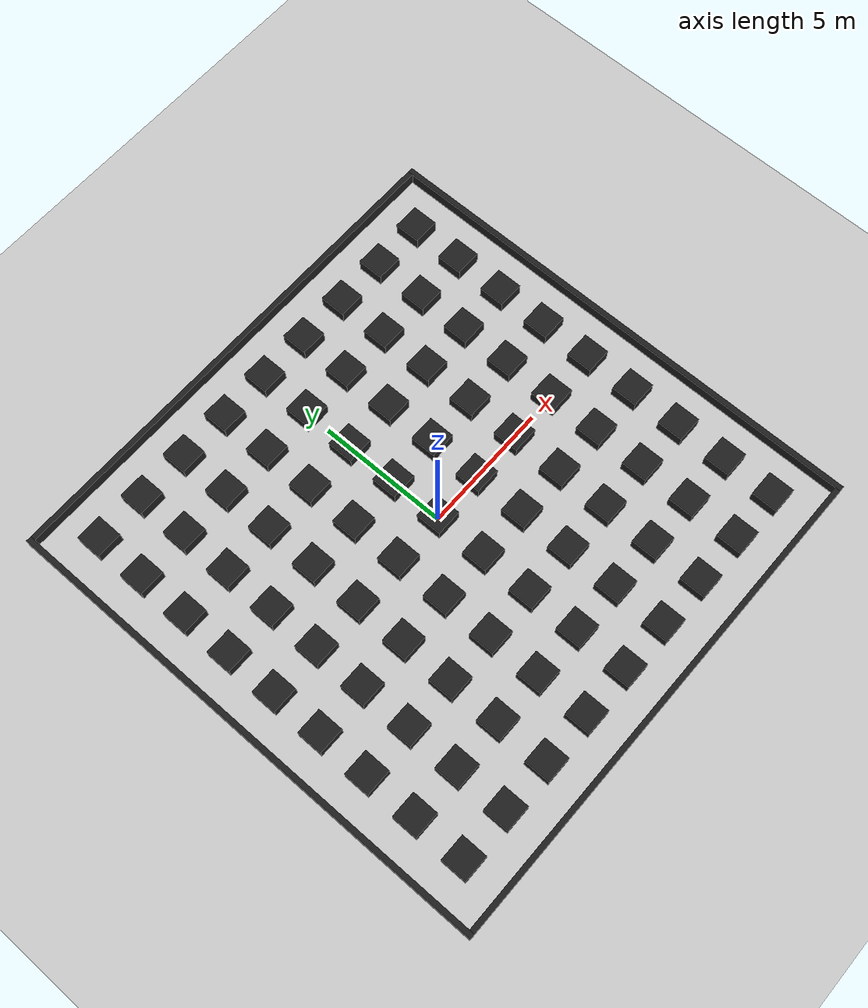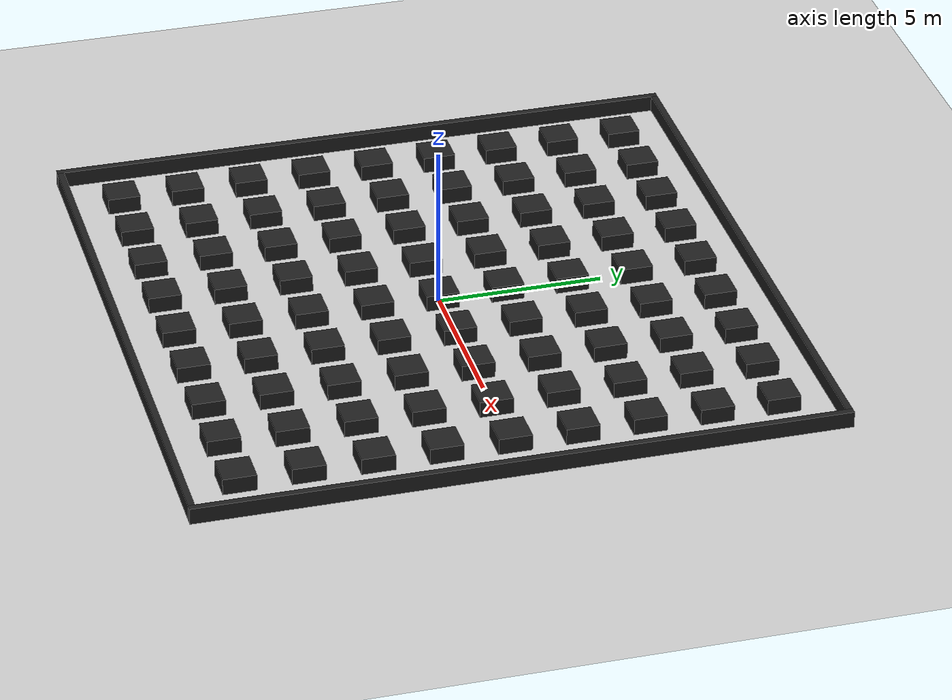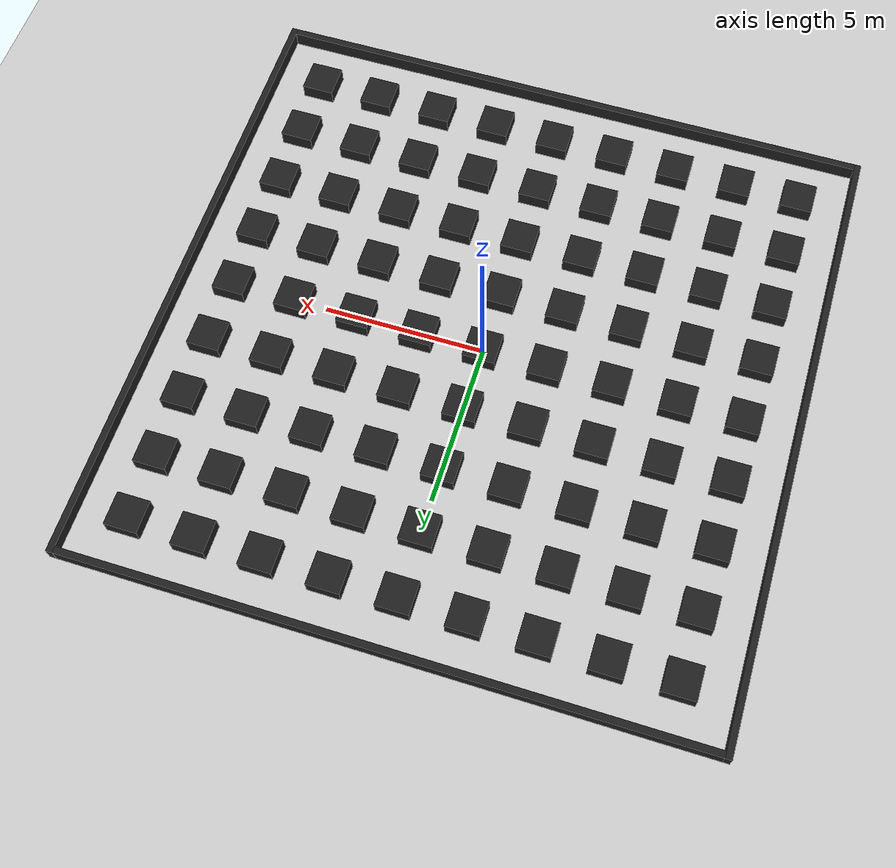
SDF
<sdf version='1.4'>
  <world name='default'>
    <!-- A global light source -->
    <include>
      <uri>model://sun</uri>
    </include>

    <!-- A ground plane -->
    <include>
      <uri>model://ground_plane</uri>
    </include>

    <physics type="ode">
      <real_time_update_rate>200.0</real_time_update_rate>
      <max_step_size>0.005</max_step_size>
      <real_time_factor>1</real_time_factor>
      <ode>
        <solver>
          <type>quick</type>
          <iters>150</iters>
          <precon_iters>0</precon_iters>
          <sor>1.400000</sor>
          <use_dynamic_moi_rescaling>1</use_dynamic_moi_rescaling>
        </solver>
        <constraints>
          <cfm>0.00001</cfm>
          <erp>0.2</erp>
          <contact_max_correcting_vel>2000.000000</contact_max_correcting_vel>
          <contact_surface_layer>0.01000</contact_surface_layer>
        </constraints>
      </ode>
    </physics>

    <include>
      <uri>model://10x10</uri>
    </include>

    <scene>
      <ambient>0.4 0.4 0.4 1</ambient>
      <background>0.7 0.7 0.7 1</background>
      <shadows>true</shadows>
    </scene>

    <gui fullscreen='0'>
      <camera name='user_camera'>
        <pose>0.0 0.0 17.0 0 1.5708 1.5708</pose>
        <view_controller>orbit</view_controller>
      </camera>
    </gui>
  </world>
</sdf>

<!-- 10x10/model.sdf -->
<sdf version='1.5'>
  <model name='10x10'>
    <static>1</static>

    <link name='Wall_EAST'>
      <collision name='Wall_EAST_Collision'>
        <pose>9.6 0 0.25 0 0 0</pose>
        <geometry>
          <box>
            <size>0.2 19.4 0.5</size>
          </box>
        </geometry>
        <surface>
          <friction>
            <ode>
              <mu>1</mu>
              <mu2>1</mu2>
              <fdir1>0 0 0</fdir1>
              <slip1>0</slip1>
              <slip2>0</slip2>
            </ode>
            <torsional>
              <coefficient>1</coefficient>
              <patch_radius>0</patch_radius>
              <surface_radius>0</surface_radius>
              <use_patch_radius>1</use_patch_radius>
              <ode>
                <slip>0</slip>
              </ode>
            </torsional>
          </friction>
          <bounce>
            <restitution_coefficient>0</restitution_coefficient>
            <threshold>1e+06</threshold>
          </bounce>
          <contact>
            <collide_without_contact>0</collide_without_contact>
            <collide_without_contact_bitmask>1</collide_without_contact_bitmask>
            <collide_bitmask>1</collide_bitmask>
            <ode>
              <soft_cfm>0</soft_cfm>
              <soft_erp>0.2</soft_erp>
              <kp>1e+13</kp>
              <kd>1</kd>
              <max_vel>0.01</max_vel>
              <min_depth>0</min_depth>
            </ode>
            <bullet>
              <split_impulse>1</split_impulse>
              <split_impulse_penetration_threshold>-0.01</split_impulse_penetration_threshold>
              <soft_cfm>0</soft_cfm>
              <soft_erp>0.2</soft_erp>
              <kp>1e+13</kp>
              <kd>1</kd>
            </bullet>
          </contact>
        </surface>
      </collision>

      <visual name='Wall_EAST_Visual'>
        <pose>9.6 0 0.25 0 0 0</pose>
        <geometry>
          <box>
            <size>0.2 19.4 0.5</size>
          </box>
        </geometry>
        <material>
          <script>
            <name>Gazebo/Black</name>
          </script>
        </material>
      </visual>
    </link>

    <link name='Wall_WEST'>
      <collision name='Wall_WEST_Collision'>
        <pose>-9.6 0 0.25 0 0 0</pose>
        <geometry>
          <box>
            <size>0.2 19.4 0.5</size>
          </box>
        </geometry>
        <surface>
          <friction>
            <ode>
              <mu>1</mu>
              <mu2>1</mu2>
              <fdir1>0 0 0</fdir1>
              <slip1>0</slip1>
              <slip2>0</slip2>
            </ode>
            <torsional>
              <coefficient>1</coefficient>
              <patch_radius>0</patch_radius>
              <surface_radius>0</surface_radius>
              <use_patch_radius>1</use_patch_radius>
              <ode>
                <slip>0</slip>
              </ode>
            </torsional>
          </friction>
          <bounce>
            <restitution_coefficient>0</restitution_coefficient>
            <threshold>1e+06</threshold>
          </bounce>
          <contact>
            <collide_without_contact>0</collide_without_contact>
            <collide_without_contact_bitmask>1</collide_without_contact_bitmask>
            <collide_bitmask>1</collide_bitmask>
            <ode>
              <soft_cfm>0</soft_cfm>
              <soft_erp>0.2</soft_erp>
              <kp>1e+13</kp>
              <kd>1</kd>
              <max_vel>0.01</max_vel>
              <min_depth>0</min_depth>
            </ode>
            <bullet>
              <split_impulse>1</split_impulse>
              <split_impulse_penetration_threshold>-0.01</split_impulse_penetration_threshold>
              <soft_cfm>0</soft_cfm>
              <soft_erp>0.2</soft_erp>
              <kp>1e+13</kp>
              <kd>1</kd>
            </bullet>
          </contact>
        </surface>
      </collision>

      <visual name='Wall_SOUTH_Visual'>
        <pose>-9.6 0 0.25 0 0 0</pose>
        <geometry>
          <box>
            <size>0.2 19.4 0.5</size>
          </box>
        </geometry>
        <material>
          <script>
            <name>Gazebo/Black</name>
          </script>
        </material>
      </visual>
    </link>

    <link name='Wall_SOUTH'>
      <collision name='Wall_SOUTH_Collision'>
        <pose>0 -9.6 0.25 0 0 0</pose>
        <geometry>
          <box>
            <size>19 0.2 0.5</size>
          </box>
        </geometry>
        <surface>
          <friction>
            <ode>
              <mu>1</mu>
              <mu2>1</mu2>
              <fdir1>0 0 0</fdir1>
              <slip1>0</slip1>
              <slip2>0</slip2>
            </ode>
            <torsional>
              <coefficient>1</coefficient>
              <patch_radius>0</patch_radius>
              <surface_radius>0</surface_radius>
              <use_patch_radius>1</use_patch_radius>
              <ode>
                <slip>0</slip>
              </ode>
            </torsional>
          </friction>
          <bounce>
            <restitution_coefficient>0</restitution_coefficient>
            <threshold>1e+06</threshold>
          </bounce>
          <contact>
            <collide_without_contact>0</collide_without_contact>
            <collide_without_contact_bitmask>1</collide_without_contact_bitmask>
            <collide_bitmask>1</collide_bitmask>
            <ode>
              <soft_cfm>0</soft_cfm>
              <soft_erp>0.2</soft_erp>
              <kp>1e+13</kp>
              <kd>1</kd>
              <max_vel>0.01</max_vel>
              <min_depth>0</min_depth>
            </ode>
            <bullet>
              <split_impulse>1</split_impulse>
              <split_impulse_penetration_threshold>-0.01</split_impulse_penetration_threshold>
              <soft_cfm>0</soft_cfm>
              <soft_erp>0.2</soft_erp>
              <kp>1e+13</kp>
              <kd>1</kd>
            </bullet>
          </contact>
        </surface>
      </collision>

      <visual name='Wall_SOUTH_Visual'>
        <pose>0 -9.6 0.25 0 0 0</pose>
        <geometry>
          <box>
            <size>19 0.2 0.5</size>
          </box>
        </geometry>
        <material>
          <script>
            <name>Gazebo/Black</name>
          </script>
        </material>
      </visual>
    </link>

    <link name='Wall_NORTH'>
      <collision name='Wall_NORTH_Collision'>
        <pose>0 9.6 0.25 0 0 0</pose>
        <geometry>
          <box>
            <size>19 0.2 0.5</size>
          </box>
        </geometry>
        <surface>
          <friction>
            <ode>
              <mu>1</mu>
              <mu2>1</mu2>
              <fdir1>0 0 0</fdir1>
              <slip1>0</slip1>
              <slip2>0</slip2>
            </ode>
            <torsional>
              <coefficient>1</coefficient>
              <patch_radius>0</patch_radius>
              <surface_radius>0</surface_radius>
              <use_patch_radius>1</use_patch_radius>
              <ode>
                <slip>0</slip>
              </ode>
            </torsional>
          </friction>
          <bounce>
            <restitution_coefficient>0</restitution_coefficient>
            <threshold>1e+06</threshold>
          </bounce>
          <contact>
            <collide_without_contact>0</collide_without_contact>
            <collide_without_contact_bitmask>1</collide_without_contact_bitmask>
            <collide_bitmask>1</collide_bitmask>
            <ode>
              <soft_cfm>0</soft_cfm>
              <soft_erp>0.2</soft_erp>
              <kp>1e+13</kp>
              <kd>1</kd>
              <max_vel>0.01</max_vel>
              <min_depth>0</min_depth>
            </ode>
            <bullet>
              <split_impulse>1</split_impulse>
              <split_impulse_penetration_threshold>-0.01</split_impulse_penetration_threshold>
              <soft_cfm>0</soft_cfm>
              <soft_erp>0.2</soft_erp>
              <kp>1e+13</kp>
              <kd>1</kd>
            </bullet>
          </contact>
        </surface>
      </collision>

      <visual name='Wall_NORTH_Visual'>
        <pose>0 9.6 0.25 0 0 0</pose>
        <geometry>
          <box>
            <size>19 0.2 0.5</size>
          </box>
        </geometry>
        <material>
          <script>
            <name>Gazebo/Black</name>
          </script>
        </material>
      </visual>
    </link>

    <!-- row 1-->
    <link name='Box1'>
      <collision name='Box1_Collision'>
        <pose>-8 8 0.25 0 0 0</pose>
        <geometry>
          <box>
            <size>1 1 0.5</size>
          </box>
        </geometry>
        <surface>
          <friction>
            <ode>
              <mu>1</mu>
              <mu2>1</mu2>
              <fdir1>0 0 0</fdir1>
              <slip1>0</slip1>
              <slip2>0</slip2>
            </ode>
            <torsional>
              <coefficient>1</coefficient>
              <patch_radius>0</patch_radius>
              <surface_radius>0</surface_radius>
              <use_patch_radius>1</use_patch_radius>
              <ode>
                <slip>0</slip>
              </ode>
            </torsional>
          </friction>
          <bounce>
            <restitution_coefficient>0</restitution_coefficient>
            <threshold>1e+06</threshold>
          </bounce>
          <contact>
            <collide_without_contact>0</collide_without_contact>
            <collide_without_contact_bitmask>1</collide_without_contact_bitmask>
            <collide_bitmask>1</collide_bitmask>
            <ode>
              <soft_cfm>0</soft_cfm>
              <soft_erp>0.2</soft_erp>
              <kp>1e+13</kp>
              <kd>1</kd>
              <max_vel>0.01</max_vel>
              <min_depth>0</min_depth>
            </ode>
            <bullet>
              <split_impulse>1</split_impulse>
              <split_impulse_penetration_threshold>-0.01</split_impulse_penetration_threshold>
              <soft_cfm>0</soft_cfm>
              <soft_erp>0.2</soft_erp>
              <kp>1e+13</kp>
              <kd>1</kd>
            </bullet>
          </contact>
        </surface>
      </collision>

      <visual name='Box1_Visual'>
        <pose>-8 8 0.25 0 0 0</pose>
        <geometry>
          <box>
            <size>1 1 0.5</size>
          </box>
        </geometry>
        <material>
          <script>
            <name>Gazebo/Black</name>
          </script>
        </material>
      </visual>
    </link>

    <link name='Box2'>
      <collision name='Box2_Collision'>
        <pose>-6 8 0.25 0 0 0</pose>
        <geometry>
          <box>
            <size>1 1 0.5</size>
          </box>
        </geometry>
        <surface>
          <friction>
            <ode>
              <mu>1</mu>
              <mu2>1</mu2>
              <fdir1>0 0 0</fdir1>
              <slip1>0</slip1>
              <slip2>0</slip2>
            </ode>
            <torsional>
              <coefficient>1</coefficient>
              <patch_radius>0</patch_radius>
              <surface_radius>0</surface_radius>
              <use_patch_radius>1</use_patch_radius>
              <ode>
                <slip>0</slip>
              </ode>
            </torsional>
          </friction>
          <bounce>
            <restitution_coefficient>0</restitution_coefficient>
            <threshold>1e+06</threshold>
          </bounce>
          <contact>
            <collide_without_contact>0</collide_without_contact>
            <collide_without_contact_bitmask>1</collide_without_contact_bitmask>
            <collide_bitmask>1</collide_bitmask>
            <ode>
              <soft_cfm>0</soft_cfm>
              <soft_erp>0.2</soft_erp>
              <kp>1e+13</kp>
              <kd>1</kd>
              <max_vel>0.01</max_vel>
              <min_depth>0</min_depth>
            </ode>
            <bullet>
              <split_impulse>1</split_impulse>
              <split_impulse_penetration_threshold>-0.01</split_impulse_penetration_threshold>
              <soft_cfm>0</soft_cfm>
              <soft_erp>0.2</soft_erp>
              <kp>1e+13</kp>
              <kd>1</kd>
            </bullet>
          </contact>
        </surface>
      </collision>

      <visual name='Box2_Visual'>
        <pose>-6 8 0.25 0 0 0</pose>
        <geometry>
          <box>
            <size>1 1 0.5</size>
          </box>
        </geometry>
        <material>
          <script>
            <name>Gazebo/Black</name>
          </script>
        </material>
      </visual>
    </link>

    <link name='Box3'>
      <collision name='Box3_Collision'>
        <pose>-4 8 0.25 0 0 0</pose>
        <geometry>
          <box>
            <size>1 1 0.5</size>
          </box>
        </geometry>
        <surface>
          <friction>
            <ode>
              <mu>1</mu>
              <mu2>1</mu2>
              <fdir1>0 0 0</fdir1>
              <slip1>0</slip1>
              <slip2>0</slip2>
            </ode>
            <torsional>
              <coefficient>1</coefficient>
              <patch_radius>0</patch_radius>
              <surface_radius>0</surface_radius>
              <use_patch_radius>1</use_patch_radius>
              <ode>
                <slip>0</slip>
              </ode>
            </torsional>
          </friction>
          <bounce>
            <restitution_coefficient>0</restitution_coefficient>
            <threshold>1e+06</threshold>
          </bounce>
          <contact>
            <collide_without_contact>0</collide_without_contact>
            <collide_without_contact_bitmask>1</collide_without_contact_bitmask>
            <collide_bitmask>1</collide_bitmask>
            <ode>
              <soft_cfm>0</soft_cfm>
              <soft_erp>0.2</soft_erp>
              <kp>1e+13</kp>
              <kd>1</kd>
              <max_vel>0.01</max_vel>
              <min_depth>0</min_depth>
            </ode>
            <bullet>
              <split_impulse>1</split_impulse>
              <split_impulse_penetration_threshold>-0.01</split_impulse_penetration_threshold>
              <soft_cfm>0</soft_cfm>
              <soft_erp>0.2</soft_erp>
              <kp>1e+13</kp>
              <kd>1</kd>
            </bullet>
          </contact>
        </surface>
      </collision>

      <visual name='Box3_Visual'>
        <pose>-4 8 0.25 0 0 0</pose>
        <geometry>
          <box>
            <size>1 1 0.5</size>
          </box>
        </geometry>
        <material>
          <script>
            <name>Gazebo/Black</name>
          </script>
        </material>
      </visual>
    </link>

    <link name='Box4'>
      <collision name='Box4_Collision'>
        <pose>-2 8 0.25 0 0 0</pose>
        <geometry>
          <box>
            <size>1 1 0.5</size>
          </box>
        </geometry>
        <surface>
          <friction>
            <ode>
              <mu>1</mu>
              <mu2>1</mu2>
              <fdir1>0 0 0</fdir1>
              <slip1>0</slip1>
              <slip2>0</slip2>
            </ode>
            <torsional>
              <coefficient>1</coefficient>
              <patch_radius>0</patch_radius>
              <surface_radius>0</surface_radius>
              <use_patch_radius>1</use_patch_radius>
              <ode>
                <slip>0</slip>
              </ode>
            </torsional>
          </friction>
          <bounce>
            <restitution_coefficient>0</restitution_coefficient>
            <threshold>1e+06</threshold>
          </bounce>
          <contact>
            <collide_without_contact>0</collide_without_contact>
            <collide_without_contact_bitmask>1</collide_without_contact_bitmask>
            <collide_bitmask>1</collide_bitmask>
            <ode>
              <soft_cfm>0</soft_cfm>
              <soft_erp>0.2</soft_erp>
              <kp>1e+13</kp>
              <kd>1</kd>
              <max_vel>0.01</max_vel>
              <min_depth>0</min_depth>
            </ode>
            <bullet>
              <split_impulse>1</split_impulse>
              <split_impulse_penetration_threshold>-0.01</split_impulse_penetration_threshold>
              <soft_cfm>0</soft_cfm>
              <soft_erp>0.2</soft_erp>
              <kp>1e+13</kp>
              <kd>1</kd>
            </bullet>
          </contact>
        </surface>
      </collision>

      <visual name='Box4_Visual'>
        <pose>-2 8 0.25 0 0 0</pose>
        <geometry>
          <box>
            <size>1 1 0.5</size>
          </box>
        </geometry>
        <material>
          <script>
            <name>Gazebo/Black</name>
          </script>
        </material>
      </visual>
    </link>

    <link name='Box5'>
      <collision name='Box5_Collision'>
        <pose>0 8 0.25 0 0 0</pose>
        <geometry>
          <box>
            <size>1 1 0.5</size>
          </box>
        </geometry>
        <surface>
          <friction>
            <ode>
              <mu>1</mu>
              <mu2>1</mu2>
              <fdir1>0 0 0</fdir1>
              <slip1>0</slip1>
              <slip2>0</slip2>
            </ode>
            <torsional>
              <coefficient>1</coefficient>
              <patch_radius>0</patch_radius>
              <surface_radius>0</surface_radius>
              <use_patch_radius>1</use_patch_radius>
              <ode>
                <slip>0</slip>
              </ode>
            </torsional>
          </friction>
          <bounce>
            <restitution_coefficient>0</restitution_coefficient>
            <threshold>1e+06</threshold>
          </bounce>
          <contact>
            <collide_without_contact>0</collide_without_contact>
            <collide_without_contact_bitmask>1</collide_without_contact_bitmask>
            <collide_bitmask>1</collide_bitmask>
            <ode>
              <soft_cfm>0</soft_cfm>
              <soft_erp>0.2</soft_erp>
              <kp>1e+13</kp>
              <kd>1</kd>
              <max_vel>0.01</max_vel>
              <min_depth>0</min_depth>
            </ode>
            <bullet>
              <split_impulse>1</split_impulse>
              <split_impulse_penetration_threshold>-0.01</split_impulse_penetration_threshold>
              <soft_cfm>0</soft_cfm>
              <soft_erp>0.2</soft_erp>
              <kp>1e+13</kp>
              <kd>1</kd>
            </bullet>
          </contact>
        </surface>
      </collision>

      <visual name='Box5_Visual'>
        <pose>0 8 0.25 0 0 0</pose>
        <geometry>
          <box>
            <size>1 1 0.5</size>
          </box>
        </geometry>
        <material>
          <script>
            <name>Gazebo/Black</name>
          </script>
        </material>
      </visual>
    </link>

    <link name='Box6'>
      <collision name='Box6_Collision'>
        <pose>2 8 0.25 0 0 0</pose>
        <geometry>
          <box>
            <size>1 1 0.5</size>
          </box>
        </geometry>
        <surface>
          <friction>
            <ode>
              <mu>1</mu>
              <mu2>1</mu2>
              <fdir1>0 0 0</fdir1>
              <slip1>0</slip1>
              <slip2>0</slip2>
            </ode>
            <torsional>
              <coefficient>1</coefficient>
              <patch_radius>0</patch_radius>
              <surface_radius>0</surface_radius>
              <use_patch_radius>1</use_patch_radius>
              <ode>
                <slip>0</slip>
              </ode>
            </torsional>
          </friction>
          <bounce>
            <restitution_coefficient>0</restitution_coefficient>
            <threshold>1e+06</threshold>
          </bounce>
          <contact>
            <collide_without_contact>0</collide_without_contact>
            <collide_without_contact_bitmask>1</collide_without_contact_bitmask>
            <collide_bitmask>1</collide_bitmask>
            <ode>
              <soft_cfm>0</soft_cfm>
              <soft_erp>0.2</soft_erp>
              <kp>1e+13</kp>
              <kd>1</kd>
              <max_vel>0.01</max_vel>
              <min_depth>0</min_depth>
            </ode>
            <bullet>
              <split_impulse>1</split_impulse>
              <split_impulse_penetration_threshold>-0.01</split_impulse_penetration_threshold>
              <soft_cfm>0</soft_cfm>
              <soft_erp>0.2</soft_erp>
              <kp>1e+13</kp>
              <kd>1</kd>
            </bullet>
          </contact>
        </surface>
      </collision>

      <visual name='Box6_Visual'>
        <pose>2 8 0.25 0 0 0</pose>
        <geometry>
          <box>
            <size>1 1 0.5</size>
          </box>
        </geometry>
        <material>
          <script>
            <name>Gazebo/Black</name>
          </script>
        </material>
      </visual>
    </link>

    <link name='Box7'>
      <collision name='Box7_Collision'>
        <pose>4 8 0.25 0 0 0</pose>
        <geometry>
          <box>
            <size>1 1 0.5</size>
          </box>
        </geometry>
        <surface>
          <friction>
            <ode>
              <mu>1</mu>
              <mu2>1</mu2>
              <fdir1>0 0 0</fdir1>
              <slip1>0</slip1>
              <slip2>0</slip2>
            </ode>
            <torsional>
              <coefficient>1</coefficient>
              <patch_radius>0</patch_radius>
              <surface_radius>0</surface_radius>
              <use_patch_radius>1</use_patch_radius>
              <ode>
                <slip>0</slip>
              </ode>
            </torsional>
          </friction>
          <bounce>
            <restitution_coefficient>0</restitution_coefficient>
            <threshold>1e+06</threshold>
          </bounce>
          <contact>
            <collide_without_contact>0</collide_without_contact>
            <collide_without_contact_bitmask>1</collide_without_contact_bitmask>
            <collide_bitmask>1</collide_bitmask>
            <ode>
              <soft_cfm>0</soft_cfm>
              <soft_erp>0.2</soft_erp>
              <kp>1e+13</kp>
              <kd>1</kd>
              <max_vel>0.01</max_vel>
              <min_depth>0</min_depth>
            </ode>
            <bullet>
              <split_impulse>1</split_impulse>
              <split_impulse_penetration_threshold>-0.01</split_impulse_penetration_threshold>
              <soft_cfm>0</soft_cfm>
              <soft_erp>0.2</soft_erp>
              <kp>1e+13</kp>
              <kd>1</kd>
            </bullet>
          </contact>
        </surface>
      </collision>

      <visual name='Box7_Visual'>
        <pose>4 8 0.25 0 0 0</pose>
        <geometry>
          <box>
            <size>1 1 0.5</size>
          </box>
        </geometry>
        <material>
          <script>
            <name>Gazebo/Black</name>
          </script>
        </material>
      </visual>
    </link>

    <link name='Box8'>
      <collision name='Box8_Collision'>
        <pose>6 8 0.25 0 0 0</pose>
        <geometry>
          <box>
            <size>1 1 0.5</size>
          </box>
        </geometry>
        <surface>
          <friction>
            <ode>
              <mu>1</mu>
              <mu2>1</mu2>
              <fdir1>0 0 0</fdir1>
              <slip1>0</slip1>
              <slip2>0</slip2>
            </ode>
            <torsional>
              <coefficient>1</coefficient>
              <patch_radius>0</patch_radius>
              <surface_radius>0</surface_radius>
              <use_patch_radius>1</use_patch_radius>
              <ode>
                <slip>0</slip>
              </ode>
            </torsional>
          </friction>
          <bounce>
            <restitution_coefficient>0</restitution_coefficient>
            <threshold>1e+06</threshold>
          </bounce>
          <contact>
            <collide_without_contact>0</collide_without_contact>
            <collide_without_contact_bitmask>1</collide_without_contact_bitmask>
            <collide_bitmask>1</collide_bitmask>
            <ode>
              <soft_cfm>0</soft_cfm>
              <soft_erp>0.2</soft_erp>
              <kp>1e+13</kp>
              <kd>1</kd>
              <max_vel>0.01</max_vel>
              <min_depth>0</min_depth>
            </ode>
            <bullet>
              <split_impulse>1</split_impulse>
              <split_impulse_penetration_threshold>-0.01</split_impulse_penetration_threshold>
              <soft_cfm>0</soft_cfm>
              <soft_erp>0.2</soft_erp>
              <kp>1e+13</kp>
              <kd>1</kd>
            </bullet>
          </contact>
        </surface>
      </collision>

      <visual name='Box8_Visual'>
        <pose>6 8 0.25 0 0 0</pose>
        <geometry>
          <box>
            <size>1 1 0.5</size>
          </box>
        </geometry>
        <material>
          <script>
            <name>Gazebo/Black</name>
          </script>
        </material>
      </visual>
    </link>

    <link name='Box9'>
      <collision name='Box9_Collision'>
        <pose>8 8 0.25 0 0 0</pose>
        <geometry>
          <box>
            <size>1 1 0.5</size>
          </box>
        </geometry>
        <surface>
          <friction>
            <ode>
              <mu>1</mu>
              <mu2>1</mu2>
              <fdir1>0 0 0</fdir1>
              <slip1>0</slip1>
              <slip2>0</slip2>
            </ode>
            <torsional>
              <coefficient>1</coefficient>
              <patch_radius>0</patch_radius>
              <surface_radius>0</surface_radius>
              <use_patch_radius>1</use_patch_radius>
              <ode>
                <slip>0</slip>
              </ode>
            </torsional>
          </friction>
          <bounce>
            <restitution_coefficient>0</restitution_coefficient>
            <threshold>1e+06</threshold>
          </bounce>
          <contact>
            <collide_without_contact>0</collide_without_contact>
            <collide_without_contact_bitmask>1</collide_without_contact_bitmask>
            <collide_bitmask>1</collide_bitmask>
            <ode>
              <soft_cfm>0</soft_cfm>
              <soft_erp>0.2</soft_erp>
              <kp>1e+13</kp>
              <kd>1</kd>
              <max_vel>0.01</max_vel>
              <min_depth>0</min_depth>
            </ode>
            <bullet>
              <split_impulse>1</split_impulse>
              <split_impulse_penetration_threshold>-0.01</split_impulse_penetration_threshold>
              <soft_cfm>0</soft_cfm>
              <soft_erp>0.2</soft_erp>
              <kp>1e+13</kp>
              <kd>1</kd>
            </bullet>
          </contact>
        </surface>
      </collision>

      <visual name='Box9_Visual'>
        <pose>8 8 0.25 0 0 0</pose>
        <geometry>
          <box>
            <size>1 1 0.5</size>
          </box>
        </geometry>
        <material>
          <script>
            <name>Gazebo/Black</name>
          </script>
        </material>
      </visual>
    </link>

    <!-- row 2-->
    <link name='Box10'>
      <collision name='Box10_Collision'>
        <pose>-8 6 0.25 0 0 0</pose>
        <geometry>
          <box>
            <size>1 1 0.5</size>
          </box>
        </geometry>
        <surface>
          <friction>
            <ode>
              <mu>1</mu>
              <mu2>1</mu2>
              <fdir1>0 0 0</fdir1>
              <slip1>0</slip1>
              <slip2>0</slip2>
            </ode>
            <torsional>
              <coefficient>1</coefficient>
              <patch_radius>0</patch_radius>
              <surface_radius>0</surface_radius>
              <use_patch_radius>1</use_patch_radius>
              <ode>
                <slip>0</slip>
              </ode>
            </torsional>
          </friction>
          <bounce>
            <restitution_coefficient>0</restitution_coefficient>
            <threshold>1e+06</threshold>
          </bounce>
          <contact>
            <collide_without_contact>0</collide_without_contact>
            <collide_without_contact_bitmask>1</collide_without_contact_bitmask>
            <collide_bitmask>1</collide_bitmask>
            <ode>
              <soft_cfm>0</soft_cfm>
              <soft_erp>0.2</soft_erp>
              <kp>1e+13</kp>
              <kd>1</kd>
              <max_vel>0.01</max_vel>
              <min_depth>0</min_depth>
            </ode>
            <bullet>
              <split_impulse>1</split_impulse>
              <split_impulse_penetration_threshold>-0.01</split_impulse_penetration_threshold>
              <soft_cfm>0</soft_cfm>
              <soft_erp>0.2</soft_erp>
              <kp>1e+13</kp>
              <kd>1</kd>
            </bullet>
          </contact>
        </surface>
      </collision>

      <visual name='Box10_Visual'>
        <pose>-8 6 0.25 0 0 0</pose>
        <geometry>
          <box>
            <size>1 1 0.5</size>
          </box>
        </geometry>
        <material>
          <script>
            <name>Gazebo/Black</name>
          </script>
        </material>
      </visual>
    </link>

    <link name='Box11'>
      <collision name='Box11_Collision'>
        <pose>-6 6 0.25 0 0 0</pose>
        <geometry>
          <box>
            <size>1 1 0.5</size>
          </box>
        </geometry>
        <surface>
          <friction>
            <ode>
              <mu>1</mu>
              <mu2>1</mu2>
              <fdir1>0 0 0</fdir1>
              <slip1>0</slip1>
              <slip2>0</slip2>
            </ode>
            <torsional>
              <coefficient>1</coefficient>
              <patch_radius>0</patch_radius>
              <surface_radius>0</surface_radius>
              <use_patch_radius>1</use_patch_radius>
              <ode>
                <slip>0</slip>
              </ode>
            </torsional>
          </friction>
          <bounce>
            <restitution_coefficient>0</restitution_coefficient>
            <threshold>1e+06</threshold>
          </bounce>
          <contact>
            <collide_without_contact>0</collide_without_contact>
            <collide_without_contact_bitmask>1</collide_without_contact_bitmask>
            <collide_bitmask>1</collide_bitmask>
            <ode>
              <soft_cfm>0</soft_cfm>
              <soft_erp>0.2</soft_erp>
              <kp>1e+13</kp>
              <kd>1</kd>
              <max_vel>0.01</max_vel>
              <min_depth>0</min_depth>
            </ode>
            <bullet>
              <split_impulse>1</split_impulse>
              <split_impulse_penetration_threshold>-0.01</split_impulse_penetration_threshold>
              <soft_cfm>0</soft_cfm>
              <soft_erp>0.2</soft_erp>
              <kp>1e+13</kp>
              <kd>1</kd>
            </bullet>
          </contact>
        </surface>
      </collision>

      <visual name='Box11_Visual'>
        <pose>-6 6 0.25 0 0 0</pose>
        <geometry>
          <box>
            <size>1 1 0.5</size>
          </box>
        </geometry>
        <material>
          <script>
            <name>Gazebo/Black</name>
          </script>
        </material>
      </visual>
    </link>

    <link name='Box12'>
      <collision name='Box12_Collision'>
        <pose>-4 6 0.25 0 0 0</pose>
        <geometry>
          <box>
            <size>1 1 0.5</size>
          </box>
        </geometry>
        <surface>
          <friction>
            <ode>
              <mu>1</mu>
              <mu2>1</mu2>
              <fdir1>0 0 0</fdir1>
              <slip1>0</slip1>
              <slip2>0</slip2>
            </ode>
            <torsional>
              <coefficient>1</coefficient>
              <patch_radius>0</patch_radius>
              <surface_radius>0</surface_radius>
              <use_patch_radius>1</use_patch_radius>
              <ode>
                <slip>0</slip>
              </ode>
            </torsional>
          </friction>
          <bounce>
            <restitution_coefficient>0</restitution_coefficient>
            <threshold>1e+06</threshold>
          </bounce>
          <contact>
            <collide_without_contact>0</collide_without_contact>
            <collide_without_contact_bitmask>1</collide_without_contact_bitmask>
            <collide_bitmask>1</collide_bitmask>
            <ode>
              <soft_cfm>0</soft_cfm>
              <soft_erp>0.2</soft_erp>
              <kp>1e+13</kp>
              <kd>1</kd>
              <max_vel>0.01</max_vel>
              <min_depth>0</min_depth>
            </ode>
            <bullet>
              <split_impulse>1</split_impulse>
              <split_impulse_penetration_threshold>-0.01</split_impulse_penetration_threshold>
              <soft_cfm>0</soft_cfm>
              <soft_erp>0.2</soft_erp>
              <kp>1e+13</kp>
              <kd>1</kd>
            </bullet>
          </contact>
        </surface>
      </collision>

      <visual name='Box12_Visual'>
        <pose>-4 6 0.25 0 0 0</pose>
        <geometry>
          <box>
            <size>1 1 0.5</size>
          </box>
        </geometry>
        <material>
          <script>
            <name>Gazebo/Black</name>
          </script>
        </material>
      </visual>
    </link>

    <link name='Box13'>
      <collision name='Box13_Collision'>
        <pose>-2 6 0.25 0 0 0</pose>
        <geometry>
          <box>
            <size>1 1 0.5</size>
          </box>
        </geometry>
        <surface>
          <friction>
            <ode>
              <mu>1</mu>
              <mu2>1</mu2>
              <fdir1>0 0 0</fdir1>
              <slip1>0</slip1>
              <slip2>0</slip2>
            </ode>
            <torsional>
              <coefficient>1</coefficient>
              <patch_radius>0</patch_radius>
              <surface_radius>0</surface_radius>
              <use_patch_radius>1</use_patch_radius>
              <ode>
                <slip>0</slip>
              </ode>
            </torsional>
          </friction>
          <bounce>
            <restitution_coefficient>0</restitution_coefficient>
            <threshold>1e+06</threshold>
          </bounce>
          <contact>
            <collide_without_contact>0</collide_without_contact>
            <collide_without_contact_bitmask>1</collide_without_contact_bitmask>
            <collide_bitmask>1</collide_bitmask>
            <ode>
              <soft_cfm>0</soft_cfm>
              <soft_erp>0.2</soft_erp>
              <kp>1e+13</kp>
              <kd>1</kd>
              <max_vel>0.01</max_vel>
              <min_depth>0</min_depth>
            </ode>
            <bullet>
              <split_impulse>1</split_impulse>
              <split_impulse_penetration_threshold>-0.01</split_impulse_penetration_threshold>
              <soft_cfm>0</soft_cfm>
              <soft_erp>0.2</soft_erp>
              <kp>1e+13</kp>
              <kd>1</kd>
            </bullet>
          </contact>
        </surface>
      </collision>

      <visual name='Box13_Visual'>
        <pose>-2 6 0.25 0 0 0</pose>
        <geometry>
          <box>
            <size>1 1 0.5</size>
          </box>
        </geometry>
        <material>
          <script>
            <name>Gazebo/Black</name>
          </script>
        </material>
      </visual>
    </link>

    <link name='Box14'>
      <collision name='Box14_Collision'>
        <pose>0 6 0.25 0 0 0</pose>
        <geometry>
          <box>
            <size>1 1 0.5</size>
          </box>
        </geometry>
        <surface>
          <friction>
            <ode>
              <mu>1</mu>
              <mu2>1</mu2>
              <fdir1>0 0 0</fdir1>
              <slip1>0</slip1>
              <slip2>0</slip2>
            </ode>
            <torsional>
              <coefficient>1</coefficient>
              <patch_radius>0</patch_radius>
              <surface_radius>0</surface_radius>
              <use_patch_radius>1</use_patch_radius>
              <ode>
                <slip>0</slip>
              </ode>
            </torsional>
          </friction>
          <bounce>
            <restitution_coefficient>0</restitution_coefficient>
            <threshold>1e+06</threshold>
          </bounce>
          <contact>
            <collide_without_contact>0</collide_without_contact>
            <collide_without_contact_bitmask>1</collide_without_contact_bitmask>
            <collide_bitmask>1</collide_bitmask>
            <ode>
              <soft_cfm>0</soft_cfm>
              <soft_erp>0.2</soft_erp>
              <kp>1e+13</kp>
              <kd>1</kd>
              <max_vel>0.01</max_vel>
              <min_depth>0</min_depth>
            </ode>
            <bullet>
              <split_impulse>1</split_impulse>
              <split_impulse_penetration_threshold>-0.01</split_impulse_penetration_threshold>
              <soft_cfm>0</soft_cfm>
              <soft_erp>0.2</soft_erp>
              <kp>1e+13</kp>
              <kd>1</kd>
            </bullet>
          </contact>
        </surface>
      </collision>

      <visual name='Box14_Visual'>
        <pose>0 6 0.25 0 0 0</pose>
        <geometry>
          <box>
            <size>1 1 0.5</size>
          </box>
        </geometry>
        <material>
          <script>
            <name>Gazebo/Black</name>
          </script>
        </material>
      </visual>
    </link>

    <link name='Box15'>
      <collision name='Box15_Collision'>
        <pose>2 6 0.25 0 0 0</pose>
        <geometry>
          <box>
            <size>1 1 0.5</size>
          </box>
        </geometry>
        <surface>
          <friction>
            <ode>
              <mu>1</mu>
              <mu2>1</mu2>
              <fdir1>0 0 0</fdir1>
              <slip1>0</slip1>
              <slip2>0</slip2>
            </ode>
            <torsional>
              <coefficient>1</coefficient>
              <patch_radius>0</patch_radius>
              <surface_radius>0</surface_radius>
              <use_patch_radius>1</use_patch_radius>
              <ode>
                <slip>0</slip>
              </ode>
            </torsional>
          </friction>
          <bounce>
            <restitution_coefficient>0</restitution_coefficient>
            <threshold>1e+06</threshold>
          </bounce>
          <contact>
            <collide_without_contact>0</collide_without_contact>
            <collide_without_contact_bitmask>1</collide_without_contact_bitmask>
            <collide_bitmask>1</collide_bitmask>
            <ode>
              <soft_cfm>0</soft_cfm>
              <soft_erp>0.2</soft_erp>
              <kp>1e+13</kp>
              <kd>1</kd>
              <max_vel>0.01</max_vel>
              <min_depth>0</min_depth>
            </ode>
            <bullet>
              <split_impulse>1</split_impulse>
              <split_impulse_penetration_threshold>-0.01</split_impulse_penetration_threshold>
              <soft_cfm>0</soft_cfm>
              <soft_erp>0.2</soft_erp>
              <kp>1e+13</kp>
              <kd>1</kd>
            </bullet>
          </contact>
        </surface>
      </collision>

      <visual name='Box15_Visual'>
        <pose>2 6 0.25 0 0 0</pose>
        <geometry>
          <box>
            <size>1 1 0.5</size>
          </box>
        </geometry>
        <material>
          <script>
            <name>Gazebo/Black</name>
          </script>
        </material>
      </visual>
    </link>

    <link name='Box16'>
      <collision name='Box16_Collision'>
        <pose>4 6 0.25 0 0 0</pose>
        <geometry>
          <box>
            <size>1 1 0.5</size>
          </box>
        </geometry>
        <surface>
          <friction>
            <ode>
              <mu>1</mu>
              <mu2>1</mu2>
              <fdir1>0 0 0</fdir1>
              <slip1>0</slip1>
              <slip2>0</slip2>
            </ode>
            <torsional>
              <coefficient>1</coefficient>
              <patch_radius>0</patch_radius>
              <surface_radius>0</surface_radius>
              <use_patch_radius>1</use_patch_radius>
              <ode>
                <slip>0</slip>
              </ode>
            </torsional>
          </friction>
          <bounce>
            <restitution_coefficient>0</restitution_coefficient>
            <threshold>1e+06</threshold>
          </bounce>
          <contact>
            <collide_without_contact>0</collide_without_contact>
            <collide_without_contact_bitmask>1</collide_without_contact_bitmask>
            <collide_bitmask>1</collide_bitmask>
            <ode>
              <soft_cfm>0</soft_cfm>
              <soft_erp>0.2</soft_erp>
              <kp>1e+13</kp>
              <kd>1</kd>
              <max_vel>0.01</max_vel>
              <min_depth>0</min_depth>
            </ode>
            <bullet>
              <split_impulse>1</split_impulse>
              <split_impulse_penetration_threshold>-0.01</split_impulse_penetration_threshold>
              <soft_cfm>0</soft_cfm>
              <soft_erp>0.2</soft_erp>
              <kp>1e+13</kp>
              <kd>1</kd>
            </bullet>
          </contact>
        </surface>
      </collision>

      <visual name='Box16_Visual'>
        <pose>4 6 0.25 0 0 0</pose>
        <geometry>
          <box>
            <size>1 1 0.5</size>
          </box>
        </geometry>
        <material>
          <script>
            <name>Gazebo/Black</name>
          </script>
        </material>
      </visual>
    </link>

    <link name='Box17'>
      <collision name='Box17_Collision'>
        <pose>6 6 0.25 0 0 0</pose>
        <geometry>
          <box>
            <size>1 1 0.5</size>
          </box>
        </geometry>
        <surface>
          <friction>
            <ode>
              <mu>1</mu>
              <mu2>1</mu2>
              <fdir1>0 0 0</fdir1>
              <slip1>0</slip1>
              <slip2>0</slip2>
            </ode>
            <torsional>
              <coefficient>1</coefficient>
              <patch_radius>0</patch_radius>
              <surface_radius>0</surface_radius>
              <use_patch_radius>1</use_patch_radius>
              <ode>
                <slip>0</slip>
              </ode>
            </torsional>
          </friction>
          <bounce>
            <restitution_coefficient>0</restitution_coefficient>
            <threshold>1e+06</threshold>
          </bounce>
          <contact>
            <collide_without_contact>0</collide_without_contact>
            <collide_without_contact_bitmask>1</collide_without_contact_bitmask>
            <collide_bitmask>1</collide_bitmask>
            <ode>
              <soft_cfm>0</soft_cfm>
              <soft_erp>0.2</soft_erp>
              <kp>1e+13</kp>
              <kd>1</kd>
              <max_vel>0.01</max_vel>
              <min_depth>0</min_depth>
            </ode>
            <bullet>
              <split_impulse>1</split_impulse>
              <split_impulse_penetration_threshold>-0.01</split_impulse_penetration_threshold>
              <soft_cfm>0</soft_cfm>
              <soft_erp>0.2</soft_erp>
              <kp>1e+13</kp>
              <kd>1</kd>
            </bullet>
          </contact>
        </surface>
      </collision>

      <visual name='Box17_Visual'>
        <pose>6 6 0.25 0 0 0</pose>
        <geometry>
          <box>
            <size>1 1 0.5</size>
          </box>
        </geometry>
        <material>
          <script>
            <name>Gazebo/Black</name>
          </script>
        </material>
      </visual>
    </link>

    <link name='Box18'>
      <collision name='Box18_Collision'>
        <pose>8 6 0.25 0 0 0</pose>
        <geometry>
          <box>
            <size>1 1 0.5</size>
          </box>
        </geometry>
        <surface>
          <friction>
            <ode>
              <mu>1</mu>
              <mu2>1</mu2>
              <fdir1>0 0 0</fdir1>
              <slip1>0</slip1>
              <slip2>0</slip2>
            </ode>
            <torsional>
              <coefficient>1</coefficient>
              <patch_radius>0</patch_radius>
              <surface_radius>0</surface_radius>
              <use_patch_radius>1</use_patch_radius>
              <ode>
                <slip>0</slip>
              </ode>
            </torsional>
          </friction>
          <bounce>
            <restitution_coefficient>0</restitution_coefficient>
            <threshold>1e+06</threshold>
          </bounce>
          <contact>
            <collide_without_contact>0</collide_without_contact>
            <collide_without_contact_bitmask>1</collide_without_contact_bitmask>
            <collide_bitmask>1</collide_bitmask>
            <ode>
              <soft_cfm>0</soft_cfm>
              <soft_erp>0.2</soft_erp>
              <kp>1e+13</kp>
              <kd>1</kd>
              <max_vel>0.01</max_vel>
              <min_depth>0</min_depth>
            </ode>
            <bullet>
              <split_impulse>1</split_impulse>
              <split_impulse_penetration_threshold>-0.01</split_impulse_penetration_threshold>
              <soft_cfm>0</soft_cfm>
              <soft_erp>0.2</soft_erp>
              <kp>1e+13</kp>
              <kd>1</kd>
            </bullet>
          </contact>
        </surface>
      </collision>

      <visual name='Box18_Visual'>
        <pose>8 6 0.25 0 0 0</pose>
        <geometry>
          <box>
            <size>1 1 0.5</size>
          </box>
        </geometry>
        <material>
          <script>
            <name>Gazebo/Black</name>
          </script>
        </material>
      </visual>
    </link>

    <!-- row 3-->
    <link name='Box19'>
      <collision name='Box19_Collision'>
        <pose>-8 4 0.25 0 0 0</pose>
        <geometry>
          <box>
            <size>1 1 0.5</size>
          </box>
        </geometry>
        <surface>
          <friction>
            <ode>
              <mu>1</mu>
              <mu2>1</mu2>
              <fdir1>0 0 0</fdir1>
              <slip1>0</slip1>
              <slip2>0</slip2>
            </ode>
            <torsional>
              <coefficient>1</coefficient>
              <patch_radius>0</patch_radius>
              <surface_radius>0</surface_radius>
              <use_patch_radius>1</use_patch_radius>
              <ode>
                <slip>0</slip>
              </ode>
            </torsional>
          </friction>
          <bounce>
            <restitution_coefficient>0</restitution_coefficient>
            <threshold>1e+06</threshold>
          </bounce>
          <contact>
            <collide_without_contact>0</collide_without_contact>
            <collide_without_contact_bitmask>1</collide_without_contact_bitmask>
            <collide_bitmask>1</collide_bitmask>
            <ode>
              <soft_cfm>0</soft_cfm>
              <soft_erp>0.2</soft_erp>
              <kp>1e+13</kp>
              <kd>1</kd>
              <max_vel>0.01</max_vel>
              <min_depth>0</min_depth>
            </ode>
            <bullet>
              <split_impulse>1</split_impulse>
              <split_impulse_penetration_threshold>-0.01</split_impulse_penetration_threshold>
              <soft_cfm>0</soft_cfm>
              <soft_erp>0.2</soft_erp>
              <kp>1e+13</kp>
              <kd>1</kd>
            </bullet>
          </contact>
        </surface>
      </collision>

      <visual name='Box19_Visual'>
        <pose>-8 4 0.25 0 0 0</pose>
        <geometry>
          <box>
            <size>1 1 0.5</size>
          </box>
        </geometry>
        <material>
          <script>
            <name>Gazebo/Black</name>
          </script>
        </material>
      </visual>
    </link>

    <link name='Box20'>
      <collision name='Box20_Collision'>
        <pose>-6 4 0.25 0 0 0</pose>
        <geometry>
          <box>
            <size>1 1 0.5</size>
          </box>
        </geometry>
        <surface>
          <friction>
            <ode>
              <mu>1</mu>
              <mu2>1</mu2>
              <fdir1>0 0 0</fdir1>
              <slip1>0</slip1>
              <slip2>0</slip2>
            </ode>
            <torsional>
              <coefficient>1</coefficient>
              <patch_radius>0</patch_radius>
              <surface_radius>0</surface_radius>
              <use_patch_radius>1</use_patch_radius>
              <ode>
                <slip>0</slip>
              </ode>
            </torsional>
          </friction>
          <bounce>
            <restitution_coefficient>0</restitution_coefficient>
            <threshold>1e+06</threshold>
          </bounce>
          <contact>
            <collide_without_contact>0</collide_without_contact>
            <collide_without_contact_bitmask>1</collide_without_contact_bitmask>
            <collide_bitmask>1</collide_bitmask>
            <ode>
              <soft_cfm>0</soft_cfm>
              <soft_erp>0.2</soft_erp>
              <kp>1e+13</kp>
              <kd>1</kd>
              <max_vel>0.01</max_vel>
              <min_depth>0</min_depth>
            </ode>
            <bullet>
              <split_impulse>1</split_impulse>
              <split_impulse_penetration_threshold>-0.01</split_impulse_penetration_threshold>
              <soft_cfm>0</soft_cfm>
              <soft_erp>0.2</soft_erp>
              <kp>1e+13</kp>
              <kd>1</kd>
            </bullet>
          </contact>
        </surface>
      </collision>

      <visual name='Box20_Visual'>
        <pose>-6 4 0.25 0 0 0</pose>
        <geometry>
          <box>
            <size>1 1 0.5</size>
          </box>
        </geometry>
        <material>
          <script>
            <name>Gazebo/Black</name>
          </script>
        </material>
      </visual>
    </link>

    <link name='Box21'>
      <collision name='Box21_Collision'>
        <pose>-4 4 0.25 0 0 0</pose>
        <geometry>
          <box>
            <size>1 1 0.5</size>
          </box>
        </geometry>
        <surface>
          <friction>
            <ode>
              <mu>1</mu>
              <mu2>1</mu2>
              <fdir1>0 0 0</fdir1>
              <slip1>0</slip1>
              <slip2>0</slip2>
            </ode>
            <torsional>
              <coefficient>1</coefficient>
              <patch_radius>0</patch_radius>
              <surface_radius>0</surface_radius>
              <use_patch_radius>1</use_patch_radius>
              <ode>
                <slip>0</slip>
              </ode>
            </torsional>
          </friction>
          <bounce>
            <restitution_coefficient>0</restitution_coefficient>
            <threshold>1e+06</threshold>
          </bounce>
          <contact>
            <collide_without_contact>0</collide_without_contact>
            <collide_without_contact_bitmask>1</collide_without_contact_bitmask>
            <collide_bitmask>1</collide_bitmask>
            <ode>
              <soft_cfm>0</soft_cfm>
              <soft_erp>0.2</soft_erp>
              <kp>1e+13</kp>
              <kd>1</kd>
              <max_vel>0.01</max_vel>
              <min_depth>0</min_depth>
            </ode>
            <bullet>
              <split_impulse>1</split_impulse>
              <split_impulse_penetration_threshold>-0.01</split_impulse_penetration_threshold>
              <soft_cfm>0</soft_cfm>
              <soft_erp>0.2</soft_erp>
              <kp>1e+13</kp>
              <kd>1</kd>
            </bullet>
          </contact>
        </surface>
      </collision>

      <visual name='Box21_Visual'>
        <pose>-4 4 0.25 0 0 0</pose>
        <geometry>
          <box>
            <size>1 1 0.5</size>
          </box>
        </geometry>
        <material>
          <script>
            <name>Gazebo/Black</name>
          </script>
        </material>
      </visual>
    </link>

    <link name='Box22'>
      <collision name='Box22_Collision'>
        <pose>-2 4 0.25 0 0 0</pose>
        <geometry>
          <box>
            <size>1 1 0.5</size>
          </box>
        </geometry>
        <surface>
          <friction>
            <ode>
              <mu>1</mu>
              <mu2>1</mu2>
              <fdir1>0 0 0</fdir1>
              <slip1>0</slip1>
              <slip2>0</slip2>
            </ode>
            <torsional>
              <coefficient>1</coefficient>
              <patch_radius>0</patch_radius>
              <surface_radius>0</surface_radius>
              <use_patch_radius>1</use_patch_radius>
              <ode>
                <slip>0</slip>
              </ode>
            </torsional>
          </friction>
          <bounce>
            <restitution_coefficient>0</restitution_coefficient>
            <threshold>1e+06</threshold>
          </bounce>
          <contact>
            <collide_without_contact>0</collide_without_contact>
            <collide_without_contact_bitmask>1</collide_without_contact_bitmask>
            <collide_bitmask>1</collide_bitmask>
            <ode>
              <soft_cfm>0</soft_cfm>
              <soft_erp>0.2</soft_erp>
              <kp>1e+13</kp>
              <kd>1</kd>
              <max_vel>0.01</max_vel>
              <min_depth>0</min_depth>
            </ode>
            <bullet>
              <split_impulse>1</split_impulse>
              <split_impulse_penetration_threshold>-0.01</split_impulse_penetration_threshold>
              <soft_cfm>0</soft_cfm>
              <soft_erp>0.2</soft_erp>
              <kp>1e+13</kp>
              <kd>1</kd>
            </bullet>
          </contact>
        </surface>
      </collision>

      <visual name='Box22_Visual'>
        <pose>-2 4 0.25 0 0 0</pose>
        <geometry>
          <box>
            <size>1 1 0.5</size>
          </box>
        </geometry>
        <material>
          <script>
            <name>Gazebo/Black</name>
          </script>
        </material>
      </visual>
    </link>

    <link name='Box23'>
      <collision name='Box23_Collision'>
        <pose>0 4 0.25 0 0 0</pose>
        <geometry>
          <box>
            <size>1 1 0.5</size>
          </box>
        </geometry>
        <surface>
          <friction>
            <ode>
              <mu>1</mu>
              <mu2>1</mu2>
              <fdir1>0 0 0</fdir1>
              <slip1>0</slip1>
              <slip2>0</slip2>
            </ode>
            <torsional>
              <coefficient>1</coefficient>
              <patch_radius>0</patch_radius>
              <surface_radius>0</surface_radius>
              <use_patch_radius>1</use_patch_radius>
              <ode>
                <slip>0</slip>
              </ode>
            </torsional>
          </friction>
          <bounce>
            <restitution_coefficient>0</restitution_coefficient>
            <threshold>1e+06</threshold>
          </bounce>
          <contact>
            <collide_without_contact>0</collide_without_contact>
            <collide_without_contact_bitmask>1</collide_without_contact_bitmask>
            <collide_bitmask>1</collide_bitmask>
            <ode>
              <soft_cfm>0</soft_cfm>
              <soft_erp>0.2</soft_erp>
              <kp>1e+13</kp>
              <kd>1</kd>
              <max_vel>0.01</max_vel>
              <min_depth>0</min_depth>
            </ode>
            <bullet>
              <split_impulse>1</split_impulse>
              <split_impulse_penetration_threshold>-0.01</split_impulse_penetration_threshold>
              <soft_cfm>0</soft_cfm>
              <soft_erp>0.2</soft_erp>
              <kp>1e+13</kp>
              <kd>1</kd>
            </bullet>
          </contact>
        </surface>
      </collision>

      <visual name='Box23_Visual'>
        <pose>0 4 0.25 0 0 0</pose>
        <geometry>
          <box>
            <size>1 1 0.5</size>
          </box>
        </geometry>
        <material>
          <script>
            <name>Gazebo/Black</name>
          </script>
        </material>
      </visual>
    </link>

    <link name='Box24'>
      <collision name='Box24_Collision'>
        <pose>2 4 0.25 0 0 0</pose>
        <geometry>
          <box>
            <size>1 1 0.5</size>
          </box>
        </geometry>
        <surface>
          <friction>
            <ode>
              <mu>1</mu>
              <mu2>1</mu2>
              <fdir1>0 0 0</fdir1>
              <slip1>0</slip1>
              <slip2>0</slip2>
            </ode>
            <torsional>
              <coefficient>1</coefficient>
              <patch_radius>0</patch_radius>
              <surface_radius>0</surface_radius>
              <use_patch_radius>1</use_patch_radius>
              <ode>
                <slip>0</slip>
              </ode>
            </torsional>
          </friction>
          <bounce>
            <restitution_coefficient>0</restitution_coefficient>
            <threshold>1e+06</threshold>
          </bounce>
          <contact>
            <collide_without_contact>0</collide_without_contact>
            <collide_without_contact_bitmask>1</collide_without_contact_bitmask>
            <collide_bitmask>1</collide_bitmask>
            <ode>
              <soft_cfm>0</soft_cfm>
              <soft_erp>0.2</soft_erp>
              <kp>1e+13</kp>
              <kd>1</kd>
              <max_vel>0.01</max_vel>
              <min_depth>0</min_depth>
            </ode>
            <bullet>
              <split_impulse>1</split_impulse>
              <split_impulse_penetration_threshold>-0.01</split_impulse_penetration_threshold>
              <soft_cfm>0</soft_cfm>
              <soft_erp>0.2</soft_erp>
              <kp>1e+13</kp>
              <kd>1</kd>
            </bullet>
          </contact>
        </surface>
      </collision>

      <visual name='Box24_Visual'>
        <pose>2 4 0.25 0 0 0</pose>
        <geometry>
          <box>
            <size>1 1 0.5</size>
          </box>
        </geometry>
        <material>
          <script>
            <name>Gazebo/Black</name>
          </script>
        </material>
      </visual>
    </link>

    <link name='Box25'>
      <collision name='Box25_Collision'>
        <pose>4 4 0.25 0 0 0</pose>
        <geometry>
          <box>
            <size>1 1 0.5</size>
          </box>
        </geometry>
        <surface>
          <friction>
            <ode>
              <mu>1</mu>
              <mu2>1</mu2>
              <fdir1>0 0 0</fdir1>
              <slip1>0</slip1>
              <slip2>0</slip2>
            </ode>
            <torsional>
              <coefficient>1</coefficient>
              <patch_radius>0</patch_radius>
              <surface_radius>0</surface_radius>
              <use_patch_radius>1</use_patch_radius>
              <ode>
                <slip>0</slip>
              </ode>
            </torsional>
          </friction>
          <bounce>
            <restitution_coefficient>0</restitution_coefficient>
            <threshold>1e+06</threshold>
          </bounce>
          <contact>
            <collide_without_contact>0</collide_without_contact>
            <collide_without_contact_bitmask>1</collide_without_contact_bitmask>
            <collide_bitmask>1</collide_bitmask>
            <ode>
              <soft_cfm>0</soft_cfm>
              <soft_erp>0.2</soft_erp>
              <kp>1e+13</kp>
              <kd>1</kd>
              <max_vel>0.01</max_vel>
              <min_depth>0</min_depth>
            </ode>
            <bullet>
              <split_impulse>1</split_impulse>
              <split_impulse_penetration_threshold>-0.01</split_impulse_penetration_threshold>
              <soft_cfm>0</soft_cfm>
              <soft_erp>0.2</soft_erp>
              <kp>1e+13</kp>
              <kd>1</kd>
            </bullet>
          </contact>
        </surface>
      </collision>

      <visual name='Box25_Visual'>
        <pose>4 4 0.25 0 0 0</pose>
        <geometry>
          <box>
            <size>1 1 0.5</size>
          </box>
        </geometry>
        <material>
          <script>
            <name>Gazebo/Black</name>
          </script>
        </material>
      </visual>
    </link>

    <link name='Box26'>
      <collision name='Box26_Collision'>
        <pose>6 4 0.25 0 0 0</pose>
        <geometry>
          <box>
            <size>1 1 0.5</size>
          </box>
        </geometry>
        <surface>
          <friction>
            <ode>
              <mu>1</mu>
              <mu2>1</mu2>
              <fdir1>0 0 0</fdir1>
              <slip1>0</slip1>
              <slip2>0</slip2>
            </ode>
            <torsional>
              <coefficient>1</coefficient>
              <patch_radius>0</patch_radius>
              <surface_radius>0</surface_radius>
              <use_patch_radius>1</use_patch_radius>
              <ode>
                <slip>0</slip>
              </ode>
            </torsional>
          </friction>
          <bounce>
            <restitution_coefficient>0</restitution_coefficient>
            <threshold>1e+06</threshold>
          </bounce>
          <contact>
            <collide_without_contact>0</collide_without_contact>
            <collide_without_contact_bitmask>1</collide_without_contact_bitmask>
            <collide_bitmask>1</collide_bitmask>
            <ode>
              <soft_cfm>0</soft_cfm>
              <soft_erp>0.2</soft_erp>
              <kp>1e+13</kp>
              <kd>1</kd>
              <max_vel>0.01</max_vel>
              <min_depth>0</min_depth>
            </ode>
            <bullet>
              <split_impulse>1</split_impulse>
              <split_impulse_penetration_threshold>-0.01</split_impulse_penetration_threshold>
              <soft_cfm>0</soft_cfm>
              <soft_erp>0.2</soft_erp>
              <kp>1e+13</kp>
              <kd>1</kd>
            </bullet>
          </contact>
        </surface>
      </collision>

      <visual name='Box26_Visual'>
        <pose>6 4 0.25 0 0 0</pose>
        <geometry>
          <box>
            <size>1 1 0.5</size>
          </box>
        </geometry>
        <material>
          <script>
            <name>Gazebo/Black</name>
          </script>
        </material>
      </visual>
    </link>

    <link name='Box27'>
      <collision name='Box27_Collision'>
        <pose>8 4 0.25 0 0 0</pose>
        <geometry>
          <box>
            <size>1 1 0.5</size>
          </box>
        </geometry>
        <surface>
          <friction>
            <ode>
              <mu>1</mu>
              <mu2>1</mu2>
              <fdir1>0 0 0</fdir1>
              <slip1>0</slip1>
              <slip2>0</slip2>
            </ode>
            <torsional>
              <coefficient>1</coefficient>
              <patch_radius>0</patch_radius>
              <surface_radius>0</surface_radius>
              <use_patch_radius>1</use_patch_radius>
              <ode>
                <slip>0</slip>
              </ode>
            </torsional>
          </friction>
          <bounce>
            <restitution_coefficient>0</restitution_coefficient>
            <threshold>1e+06</threshold>
          </bounce>
          <contact>
            <collide_without_contact>0</collide_without_contact>
            <collide_without_contact_bitmask>1</collide_without_contact_bitmask>
            <collide_bitmask>1</collide_bitmask>
            <ode>
              <soft_cfm>0</soft_cfm>
              <soft_erp>0.2</soft_erp>
              <kp>1e+13</kp>
              <kd>1</kd>
              <max_vel>0.01</max_vel>
              <min_depth>0</min_depth>
            </ode>
            <bullet>
              <split_impulse>1</split_impulse>
              <split_impulse_penetration_threshold>-0.01</split_impulse_penetration_threshold>
              <soft_cfm>0</soft_cfm>
              <soft_erp>0.2</soft_erp>
              <kp>1e+13</kp>
              <kd>1</kd>
            </bullet>
          </contact>
        </surface>
      </collision>

      <visual name='Box27_Visual'>
        <pose>8 4 0.25 0 0 0</pose>
        <geometry>
          <box>
            <size>1 1 0.5</size>
          </box>
        </geometry>
        <material>
          <script>
            <name>Gazebo/Black</name>
          </script>
        </material>
      </visual>
    </link>

    <!-- row 4-->
    <link name='Box28'>
      <collision name='Box28_Collision'>
        <pose>-8 2 0.25 0 0 0</pose>
        <geometry>
          <box>
            <size>1 1 0.5</size>
          </box>
        </geometry>
        <surface>
          <friction>
            <ode>
              <mu>1</mu>
              <mu2>1</mu2>
              <fdir1>0 0 0</fdir1>
              <slip1>0</slip1>
              <slip2>0</slip2>
            </ode>
            <torsional>
              <coefficient>1</coefficient>
              <patch_radius>0</patch_radius>
              <surface_radius>0</surface_radius>
              <use_patch_radius>1</use_patch_radius>
              <ode>
                <slip>0</slip>
              </ode>
            </torsional>
          </friction>
          <bounce>
            <restitution_coefficient>0</restitution_coefficient>
            <threshold>1e+06</threshold>
          </bounce>
          <contact>
            <collide_without_contact>0</collide_without_contact>
            <collide_without_contact_bitmask>1</collide_without_contact_bitmask>
            <collide_bitmask>1</collide_bitmask>
            <ode>
              <soft_cfm>0</soft_cfm>
              <soft_erp>0.2</soft_erp>
              <kp>1e+13</kp>
              <kd>1</kd>
              <max_vel>0.01</max_vel>
              <min_depth>0</min_depth>
            </ode>
            <bullet>
              <split_impulse>1</split_impulse>
              <split_impulse_penetration_threshold>-0.01</split_impulse_penetration_threshold>
              <soft_cfm>0</soft_cfm>
              <soft_erp>0.2</soft_erp>
              <kp>1e+13</kp>
              <kd>1</kd>
            </bullet>
          </contact>
        </surface>
      </collision>

      <visual name='Box28_Visual'>
        <pose>-8 2 0.25 0 0 0</pose>
        <geometry>
          <box>
            <size>1 1 0.5</size>
          </box>
        </geometry>
        <material>
          <script>
            <name>Gazebo/Black</name>
          </script>
        </material>
      </visual>
    </link>

    <link name='Box29'>
      <collision name='Box29_Collision'>
        <pose>-6 2 0.25 0 0 0</pose>
        <geometry>
          <box>
            <size>1 1 0.5</size>
          </box>
        </geometry>
        <surface>
          <friction>
            <ode>
              <mu>1</mu>
              <mu2>1</mu2>
              <fdir1>0 0 0</fdir1>
              <slip1>0</slip1>
              <slip2>0</slip2>
            </ode>
            <torsional>
              <coefficient>1</coefficient>
              <patch_radius>0</patch_radius>
              <surface_radius>0</surface_radius>
              <use_patch_radius>1</use_patch_radius>
              <ode>
                <slip>0</slip>
              </ode>
            </torsional>
          </friction>
          <bounce>
            <restitution_coefficient>0</restitution_coefficient>
            <threshold>1e+06</threshold>
          </bounce>
          <contact>
            <collide_without_contact>0</collide_without_contact>
            <collide_without_contact_bitmask>1</collide_without_contact_bitmask>
            <collide_bitmask>1</collide_bitmask>
            <ode>
              <soft_cfm>0</soft_cfm>
              <soft_erp>0.2</soft_erp>
              <kp>1e+13</kp>
              <kd>1</kd>
              <max_vel>0.01</max_vel>
              <min_depth>0</min_depth>
            </ode>
            <bullet>
              <split_impulse>1</split_impulse>
              <split_impulse_penetration_threshold>-0.01</split_impulse_penetration_threshold>
              <soft_cfm>0</soft_cfm>
              <soft_erp>0.2</soft_erp>
              <kp>1e+13</kp>
              <kd>1</kd>
            </bullet>
          </contact>
        </surface>
      </collision>

      <visual name='Box29_Visual'>
        <pose>-6 2 0.25 0 0 0</pose>
        <geometry>
          <box>
            <size>1 1 0.5</size>
          </box>
        </geometry>
        <material>
          <script>
            <name>Gazebo/Black</name>
          </script>
        </material>
      </visual>
    </link>

    <link name='Box30'>
      <collision name='Box30_Collision'>
        <pose>-4 2 0.25 0 0 0</pose>
        <geometry>
          <box>
            <size>1 1 0.5</size>
          </box>
        </geometry>
        <surface>
          <friction>
            <ode>
              <mu>1</mu>
              <mu2>1</mu2>
              <fdir1>0 0 0</fdir1>
              <slip1>0</slip1>
              <slip2>0</slip2>
            </ode>
            <torsional>
              <coefficient>1</coefficient>
              <patch_radius>0</patch_radius>
              <surface_radius>0</surface_radius>
              <use_patch_radius>1</use_patch_radius>
              <ode>
                <slip>0</slip>
              </ode>
            </torsional>
          </friction>
          <bounce>
            <restitution_coefficient>0</restitution_coefficient>
            <threshold>1e+06</threshold>
          </bounce>
          <contact>
            <collide_without_contact>0</collide_without_contact>
            <collide_without_contact_bitmask>1</collide_without_contact_bitmask>
            <collide_bitmask>1</collide_bitmask>
            <ode>
              <soft_cfm>0</soft_cfm>
              <soft_erp>0.2</soft_erp>
              <kp>1e+13</kp>
              <kd>1</kd>
              <max_vel>0.01</max_vel>
              <min_depth>0</min_depth>
            </ode>
            <bullet>
              <split_impulse>1</split_impulse>
              <split_impulse_penetration_threshold>-0.01</split_impulse_penetration_threshold>
              <soft_cfm>0</soft_cfm>
              <soft_erp>0.2</soft_erp>
              <kp>1e+13</kp>
              <kd>1</kd>
            </bullet>
          </contact>
        </surface>
      </collision>

      <visual name='Box30_Visual'>
        <pose>-4 2 0.25 0 0 0</pose>
        <geometry>
          <box>
            <size>1 1 0.5</size>
          </box>
        </geometry>
        <material>
          <script>
            <name>Gazebo/Black</name>
          </script>
        </material>
      </visual>
    </link>

    <link name='Box31'>
      <collision name='Box31_Collision'>
        <pose>-2 2 0.25 0 0 0</pose>
        <geometry>
          <box>
            <size>1 1 0.5</size>
          </box>
        </geometry>
        <surface>
          <friction>
            <ode>
              <mu>1</mu>
              <mu2>1</mu2>
              <fdir1>0 0 0</fdir1>
              <slip1>0</slip1>
              <slip2>0</slip2>
            </ode>
            <torsional>
              <coefficient>1</coefficient>
              <patch_radius>0</patch_radius>
              <surface_radius>0</surface_radius>
              <use_patch_radius>1</use_patch_radius>
              <ode>
                <slip>0</slip>
              </ode>
            </torsional>
          </friction>
          <bounce>
            <restitution_coefficient>0</restitution_coefficient>
            <threshold>1e+06</threshold>
          </bounce>
          <contact>
            <collide_without_contact>0</collide_without_contact>
            <collide_without_contact_bitmask>1</collide_without_contact_bitmask>
            <collide_bitmask>1</collide_bitmask>
            <ode>
              <soft_cfm>0</soft_cfm>
              <soft_erp>0.2</soft_erp>
              <kp>1e+13</kp>
              <kd>1</kd>
              <max_vel>0.01</max_vel>
              <min_depth>0</min_depth>
            </ode>
            <bullet>
              <split_impulse>1</split_impulse>
              <split_impulse_penetration_threshold>-0.01</split_impulse_penetration_threshold>
              <soft_cfm>0</soft_cfm>
              <soft_erp>0.2</soft_erp>
              <kp>1e+13</kp>
              <kd>1</kd>
            </bullet>
          </contact>
        </surface>
      </collision>

      <visual name='Box31_Visual'>
        <pose>-2 2 0.25 0 0 0</pose>
        <geometry>
          <box>
            <size>1 1 0.5</size>
          </box>
        </geometry>
        <material>
          <script>
            <name>Gazebo/Black</name>
          </script>
        </material>
      </visual>
    </link>

    <link name='Box32'>
      <collision name='Box32_Collision'>
        <pose>0 2 0.25 0 0 0</pose>
        <geometry>
          <box>
            <size>1 1 0.5</size>
          </box>
        </geometry>
        <surface>
          <friction>
            <ode>
              <mu>1</mu>
              <mu2>1</mu2>
              <fdir1>0 0 0</fdir1>
              <slip1>0</slip1>
              <slip2>0</slip2>
            </ode>
            <torsional>
              <coefficient>1</coefficient>
              <patch_radius>0</patch_radius>
              <surface_radius>0</surface_radius>
              <use_patch_radius>1</use_patch_radius>
              <ode>
                <slip>0</slip>
              </ode>
            </torsional>
          </friction>
          <bounce>
            <restitution_coefficient>0</restitution_coefficient>
            <threshold>1e+06</threshold>
          </bounce>
          <contact>
            <collide_without_contact>0</collide_without_contact>
            <collide_without_contact_bitmask>1</collide_without_contact_bitmask>
            <collide_bitmask>1</collide_bitmask>
            <ode>
              <soft_cfm>0</soft_cfm>
              <soft_erp>0.2</soft_erp>
              <kp>1e+13</kp>
              <kd>1</kd>
              <max_vel>0.01</max_vel>
              <min_depth>0</min_depth>
            </ode>
            <bullet>
              <split_impulse>1</split_impulse>
              <split_impulse_penetration_threshold>-0.01</split_impulse_penetration_threshold>
              <soft_cfm>0</soft_cfm>
              <soft_erp>0.2</soft_erp>
              <kp>1e+13</kp>
              <kd>1</kd>
            </bullet>
          </contact>
        </surface>
      </collision>

      <visual name='Box32_Visual'>
        <pose>0 2 0.25 0 0 0</pose>
        <geometry>
          <box>
            <size>1 1 0.5</size>
          </box>
        </geometry>
        <material>
          <script>
            <name>Gazebo/Black</name>
          </script>
        </material>
      </visual>
    </link>

    <link name='Box33'>
      <collision name='Box33_Collision'>
        <pose>2 2 0.25 0 0 0</pose>
        <geometry>
          <box>
            <size>1 1 0.5</size>
          </box>
        </geometry>
        <surface>
          <friction>
            <ode>
              <mu>1</mu>
              <mu2>1</mu2>
              <fdir1>0 0 0</fdir1>
              <slip1>0</slip1>
              <slip2>0</slip2>
            </ode>
            <torsional>
              <coefficient>1</coefficient>
              <patch_radius>0</patch_radius>
              <surface_radius>0</surface_radius>
              <use_patch_radius>1</use_patch_radius>
              <ode>
                <slip>0</slip>
              </ode>
            </torsional>
          </friction>
          <bounce>
            <restitution_coefficient>0</restitution_coefficient>
            <threshold>1e+06</threshold>
          </bounce>
          <contact>
            <collide_without_contact>0</collide_without_contact>
            <collide_without_contact_bitmask>1</collide_without_contact_bitmask>
            <collide_bitmask>1</collide_bitmask>
            <ode>
              <soft_cfm>0</soft_cfm>
              <soft_erp>0.2</soft_erp>
              <kp>1e+13</kp>
              <kd>1</kd>
              <max_vel>0.01</max_vel>
              <min_depth>0</min_depth>
            </ode>
            <bullet>
              <split_impulse>1</split_impulse>
              <split_impulse_penetration_threshold>-0.01</split_impulse_penetration_threshold>
              <soft_cfm>0</soft_cfm>
              <soft_erp>0.2</soft_erp>
              <kp>1e+13</kp>
              <kd>1</kd>
            </bullet>
          </contact>
        </surface>
      </collision>

      <visual name='Box33_Visual'>
        <pose>2 2 0.25 0 0 0</pose>
        <geometry>
          <box>
            <size>1 1 0.5</size>
          </box>
        </geometry>
        <material>
          <script>
            <name>Gazebo/Black</name>
          </script>
        </material>
      </visual>
    </link>

    <link name='Box34'>
      <collision name='Box34_Collision'>
        <pose>4 2 0.25 0 0 0</pose>
        <geometry>
          <box>
            <size>1 1 0.5</size>
          </box>
        </geometry>
        <surface>
          <friction>
            <ode>
              <mu>1</mu>
              <mu2>1</mu2>
              <fdir1>0 0 0</fdir1>
              <slip1>0</slip1>
              <slip2>0</slip2>
            </ode>
            <torsional>
              <coefficient>1</coefficient>
              <patch_radius>0</patch_radius>
              <surface_radius>0</surface_radius>
              <use_patch_radius>1</use_patch_radius>
              <ode>
                <slip>0</slip>
              </ode>
            </torsional>
          </friction>
          <bounce>
            <restitution_coefficient>0</restitution_coefficient>
            <threshold>1e+06</threshold>
          </bounce>
          <contact>
            <collide_without_contact>0</collide_without_contact>
            <collide_without_contact_bitmask>1</collide_without_contact_bitmask>
            <collide_bitmask>1</collide_bitmask>
            <ode>
              <soft_cfm>0</soft_cfm>
              <soft_erp>0.2</soft_erp>
              <kp>1e+13</kp>
              <kd>1</kd>
              <max_vel>0.01</max_vel>
              <min_depth>0</min_depth>
            </ode>
            <bullet>
              <split_impulse>1</split_impulse>
              <split_impulse_penetration_threshold>-0.01</split_impulse_penetration_threshold>
              <soft_cfm>0</soft_cfm>
              <soft_erp>0.2</soft_erp>
              <kp>1e+13</kp>
              <kd>1</kd>
            </bullet>
          </contact>
        </surface>
      </collision>

      <visual name='Box34_Visual'>
        <pose>4 2 0.25 0 0 0</pose>
        <geometry>
          <box>
            <size>1 1 0.5</size>
          </box>
        </geometry>
        <material>
          <script>
            <name>Gazebo/Black</name>
          </script>
        </material>
      </visual>
    </link>

    <link name='Box35'>
      <collision name='Box35_Collision'>
        <pose>6 2 0.25 0 0 0</pose>
        <geometry>
          <box>
            <size>1 1 0.5</size>
          </box>
        </geometry>
        <surface>
          <friction>
            <ode>
              <mu>1</mu>
              <mu2>1</mu2>
              <fdir1>0 0 0</fdir1>
              <slip1>0</slip1>
              <slip2>0</slip2>
            </ode>
            <torsional>
              <coefficient>1</coefficient>
              <patch_radius>0</patch_radius>
              <surface_radius>0</surface_radius>
              <use_patch_radius>1</use_patch_radius>
              <ode>
                <slip>0</slip>
              </ode>
            </torsional>
          </friction>
          <bounce>
            <restitution_coefficient>0</restitution_coefficient>
            <threshold>1e+06</threshold>
          </bounce>
          <contact>
            <collide_without_contact>0</collide_without_contact>
            <collide_without_contact_bitmask>1</collide_without_contact_bitmask>
            <collide_bitmask>1</collide_bitmask>
            <ode>
              <soft_cfm>0</soft_cfm>
              <soft_erp>0.2</soft_erp>
              <kp>1e+13</kp>
              <kd>1</kd>
              <max_vel>0.01</max_vel>
              <min_depth>0</min_depth>
            </ode>
            <bullet>
              <split_impulse>1</split_impulse>
              <split_impulse_penetration_threshold>-0.01</split_impulse_penetration_threshold>
              <soft_cfm>0</soft_cfm>
              <soft_erp>0.2</soft_erp>
              <kp>1e+13</kp>
              <kd>1</kd>
            </bullet>
          </contact>
        </surface>
      </collision>

      <visual name='Box35_Visual'>
        <pose>6 2 0.25 0 0 0</pose>
        <geometry>
          <box>
            <size>1 1 0.5</size>
          </box>
        </geometry>
        <material>
          <script>
            <name>Gazebo/Black</name>
          </script>
        </material>
      </visual>
    </link>

    <link name='Box36'>
      <collision name='Box36_Collision'>
        <pose>8 2 0.25 0 0 0</pose>
        <geometry>
          <box>
            <size>1 1 0.5</size>
          </box>
        </geometry>
        <surface>
          <friction>
            <ode>
              <mu>1</mu>
              <mu2>1</mu2>
              <fdir1>0 0 0</fdir1>
              <slip1>0</slip1>
              <slip2>0</slip2>
            </ode>
            <torsional>
              <coefficient>1</coefficient>
              <patch_radius>0</patch_radius>
              <surface_radius>0</surface_radius>
              <use_patch_radius>1</use_patch_radius>
              <ode>
                <slip>0</slip>
              </ode>
            </torsional>
          </friction>
          <bounce>
            <restitution_coefficient>0</restitution_coefficient>
            <threshold>1e+06</threshold>
          </bounce>
          <contact>
            <collide_without_contact>0</collide_without_contact>
            <collide_without_contact_bitmask>1</collide_without_contact_bitmask>
            <collide_bitmask>1</collide_bitmask>
            <ode>
              <soft_cfm>0</soft_cfm>
              <soft_erp>0.2</soft_erp>
              <kp>1e+13</kp>
              <kd>1</kd>
              <max_vel>0.01</max_vel>
              <min_depth>0</min_depth>
            </ode>
            <bullet>
              <split_impulse>1</split_impulse>
              <split_impulse_penetration_threshold>-0.01</split_impulse_penetration_threshold>
              <soft_cfm>0</soft_cfm>
              <soft_erp>0.2</soft_erp>
              <kp>1e+13</kp>
              <kd>1</kd>
            </bullet>
          </contact>
        </surface>
      </collision>

      <visual name='Box36_Visual'>
        <pose>8 2 0.25 0 0 0</pose>
        <geometry>
          <box>
            <size>1 1 0.5</size>
          </box>
        </geometry>
        <material>
          <script>
            <name>Gazebo/Black</name>
          </script>
        </material>
      </visual>
    </link>

    <!-- row 5-->
    <link name='Box37'>
      <collision name='Box37_Collision'>
        <pose>-8 0 0.25 0 0 0</pose>
        <geometry>
          <box>
            <size>1 1 0.5</size>
          </box>
        </geometry>
        <surface>
          <friction>
            <ode>
              <mu>1</mu>
              <mu2>1</mu2>
              <fdir1>0 0 0</fdir1>
              <slip1>0</slip1>
              <slip2>0</slip2>
            </ode>
            <torsional>
              <coefficient>1</coefficient>
              <patch_radius>0</patch_radius>
              <surface_radius>0</surface_radius>
              <use_patch_radius>1</use_patch_radius>
              <ode>
                <slip>0</slip>
              </ode>
            </torsional>
          </friction>
          <bounce>
            <restitution_coefficient>0</restitution_coefficient>
            <threshold>1e+06</threshold>
          </bounce>
          <contact>
            <collide_without_contact>0</collide_without_contact>
            <collide_without_contact_bitmask>1</collide_without_contact_bitmask>
            <collide_bitmask>1</collide_bitmask>
            <ode>
              <soft_cfm>0</soft_cfm>
              <soft_erp>0.2</soft_erp>
              <kp>1e+13</kp>
              <kd>1</kd>
              <max_vel>0.01</max_vel>
              <min_depth>0</min_depth>
            </ode>
            <bullet>
              <split_impulse>1</split_impulse>
              <split_impulse_penetration_threshold>-0.01</split_impulse_penetration_threshold>
              <soft_cfm>0</soft_cfm>
              <soft_erp>0.2</soft_erp>
              <kp>1e+13</kp>
              <kd>1</kd>
            </bullet>
          </contact>
        </surface>
      </collision>

      <visual name='Box37_Visual'>
        <pose>-8 0 0.25 0 0 0</pose>
        <geometry>
          <box>
            <size>1 1 0.5</size>
          </box>
        </geometry>
        <material>
          <script>
            <name>Gazebo/Black</name>
          </script>
        </material>
      </visual>
    </link>

    <link name='Box38'>
      <collision name='Box38_Collision'>
        <pose>-6 0 0.25 0 0 0</pose>
        <geometry>
          <box>
            <size>1 1 0.5</size>
          </box>
        </geometry>
        <surface>
          <friction>
            <ode>
              <mu>1</mu>
              <mu2>1</mu2>
              <fdir1>0 0 0</fdir1>
              <slip1>0</slip1>
              <slip2>0</slip2>
            </ode>
            <torsional>
              <coefficient>1</coefficient>
              <patch_radius>0</patch_radius>
              <surface_radius>0</surface_radius>
              <use_patch_radius>1</use_patch_radius>
              <ode>
                <slip>0</slip>
              </ode>
            </torsional>
          </friction>
          <bounce>
            <restitution_coefficient>0</restitution_coefficient>
            <threshold>1e+06</threshold>
          </bounce>
          <contact>
            <collide_without_contact>0</collide_without_contact>
            <collide_without_contact_bitmask>1</collide_without_contact_bitmask>
            <collide_bitmask>1</collide_bitmask>
            <ode>
              <soft_cfm>0</soft_cfm>
              <soft_erp>0.2</soft_erp>
              <kp>1e+13</kp>
              <kd>1</kd>
              <max_vel>0.01</max_vel>
              <min_depth>0</min_depth>
            </ode>
            <bullet>
              <split_impulse>1</split_impulse>
              <split_impulse_penetration_threshold>-0.01</split_impulse_penetration_threshold>
              <soft_cfm>0</soft_cfm>
              <soft_erp>0.2</soft_erp>
              <kp>1e+13</kp>
              <kd>1</kd>
            </bullet>
          </contact>
        </surface>
      </collision>

      <visual name='Box38_Visual'>
        <pose>-6 0 0.25 0 0 0</pose>
        <geometry>
          <box>
            <size>1 1 0.5</size>
          </box>
        </geometry>
        <material>
          <script>
            <name>Gazebo/Black</name>
          </script>
        </material>
      </visual>
    </link>

    <link name='Box39'>
      <collision name='Box39_Collision'>
        <pose>-4 0 0.25 0 0 0</pose>
        <geometry>
          <box>
            <size>1 1 0.5</size>
          </box>
        </geometry>
        <surface>
          <friction>
            <ode>
              <mu>1</mu>
              <mu2>1</mu2>
              <fdir1>0 0 0</fdir1>
              <slip1>0</slip1>
              <slip2>0</slip2>
            </ode>
            <torsional>
              <coefficient>1</coefficient>
              <patch_radius>0</patch_radius>
              <surface_radius>0</surface_radius>
              <use_patch_radius>1</use_patch_radius>
              <ode>
                <slip>0</slip>
              </ode>
            </torsional>
          </friction>
          <bounce>
            <restitution_coefficient>0</restitution_coefficient>
            <threshold>1e+06</threshold>
          </bounce>
          <contact>
            <collide_without_contact>0</collide_without_contact>
            <collide_without_contact_bitmask>1</collide_without_contact_bitmask>
            <collide_bitmask>1</collide_bitmask>
            <ode>
              <soft_cfm>0</soft_cfm>
              <soft_erp>0.2</soft_erp>
              <kp>1e+13</kp>
              <kd>1</kd>
              <max_vel>0.01</max_vel>
              <min_depth>0</min_depth>
            </ode>
            <bullet>
              <split_impulse>1</split_impulse>
              <split_impulse_penetration_threshold>-0.01</split_impulse_penetration_threshold>
              <soft_cfm>0</soft_cfm>
              <soft_erp>0.2</soft_erp>
              <kp>1e+13</kp>
              <kd>1</kd>
            </bullet>
          </contact>
        </surface>
      </collision>

      <visual name='Box39_Visual'>
        <pose>-4 0 0.25 0 0 0</pose>
        <geometry>
          <box>
            <size>1 1 0.5</size>
          </box>
        </geometry>
        <material>
          <script>
            <name>Gazebo/Black</name>
          </script>
        </material>
      </visual>
    </link>

    <link name='Box40'>
      <collision name='Box40_Collision'>
        <pose>-2 0 0.25 0 0 0</pose>
        <geometry>
          <box>
            <size>1 1 0.5</size>
          </box>
        </geometry>
        <surface>
          <friction>
            <ode>
              <mu>1</mu>
              <mu2>1</mu2>
              <fdir1>0 0 0</fdir1>
              <slip1>0</slip1>
              <slip2>0</slip2>
            </ode>
            <torsional>
              <coefficient>1</coefficient>
              <patch_radius>0</patch_radius>
              <surface_radius>0</surface_radius>
              <use_patch_radius>1</use_patch_radius>
              <ode>
                <slip>0</slip>
              </ode>
            </torsional>
          </friction>
          <bounce>
            <restitution_coefficient>0</restitution_coefficient>
            <threshold>1e+06</threshold>
          </bounce>
          <contact>
            <collide_without_contact>0</collide_without_contact>
            <collide_without_contact_bitmask>1</collide_without_contact_bitmask>
            <collide_bitmask>1</collide_bitmask>
            <ode>
              <soft_cfm>0</soft_cfm>
              <soft_erp>0.2</soft_erp>
              <kp>1e+13</kp>
              <kd>1</kd>
              <max_vel>0.01</max_vel>
              <min_depth>0</min_depth>
            </ode>
            <bullet>
              <split_impulse>1</split_impulse>
              <split_impulse_penetration_threshold>-0.01</split_impulse_penetration_threshold>
              <soft_cfm>0</soft_cfm>
              <soft_erp>0.2</soft_erp>
              <kp>1e+13</kp>
              <kd>1</kd>
            </bullet>
          </contact>
        </surface>
      </collision>

      <visual name='Box40_Visual'>
        <pose>-2 0 0.25 0 0 0</pose>
        <geometry>
          <box>
            <size>1 1 0.5</size>
          </box>
        </geometry>
        <material>
          <script>
            <name>Gazebo/Black</name>
          </script>
        </material>
      </visual>
    </link>

    <link name='Box41'>
      <collision name='Box41_Collision'>
        <pose>0 0 0.25 0 0 0</pose>
        <geometry>
          <box>
            <size>1 1 0.5</size>
          </box>
        </geometry>
        <surface>
          <friction>
            <ode>
              <mu>1</mu>
              <mu2>1</mu2>
              <fdir1>0 0 0</fdir1>
              <slip1>0</slip1>
              <slip2>0</slip2>
            </ode>
            <torsional>
              <coefficient>1</coefficient>
              <patch_radius>0</patch_radius>
              <surface_radius>0</surface_radius>
              <use_patch_radius>1</use_patch_radius>
              <ode>
                <slip>0</slip>
              </ode>
            </torsional>
          </friction>
          <bounce>
            <restitution_coefficient>0</restitution_coefficient>
            <threshold>1e+06</threshold>
          </bounce>
          <contact>
            <collide_without_contact>0</collide_without_contact>
            <collide_without_contact_bitmask>1</collide_without_contact_bitmask>
            <collide_bitmask>1</collide_bitmask>
            <ode>
              <soft_cfm>0</soft_cfm>
              <soft_erp>0.2</soft_erp>
              <kp>1e+13</kp>
              <kd>1</kd>
              <max_vel>0.01</max_vel>
              <min_depth>0</min_depth>
            </ode>
            <bullet>
              <split_impulse>1</split_impulse>
              <split_impulse_penetration_threshold>-0.01</split_impulse_penetration_threshold>
              <soft_cfm>0</soft_cfm>
              <soft_erp>0.2</soft_erp>
              <kp>1e+13</kp>
              <kd>1</kd>
            </bullet>
          </contact>
        </surface>
      </collision>

      <visual name='Box41_Visual'>
        <pose>0 0 0.25 0 0 0</pose>
        <geometry>
          <box>
            <size>1 1 0.5</size>
          </box>
        </geometry>
        <material>
          <script>
            <name>Gazebo/Black</name>
          </script>
        </material>
      </visual>
    </link>

    <link name='Box42'>
      <collision name='Box42_Collision'>
        <pose>2 0 0.25 0 0 0</pose>
        <geometry>
          <box>
            <size>1 1 0.5</size>
          </box>
        </geometry>
        <surface>
          <friction>
            <ode>
              <mu>1</mu>
              <mu2>1</mu2>
              <fdir1>0 0 0</fdir1>
              <slip1>0</slip1>
              <slip2>0</slip2>
            </ode>
            <torsional>
              <coefficient>1</coefficient>
              <patch_radius>0</patch_radius>
              <surface_radius>0</surface_radius>
              <use_patch_radius>1</use_patch_radius>
              <ode>
                <slip>0</slip>
              </ode>
            </torsional>
          </friction>
          <bounce>
            <restitution_coefficient>0</restitution_coefficient>
            <threshold>1e+06</threshold>
          </bounce>
          <contact>
            <collide_without_contact>0</collide_without_contact>
            <collide_without_contact_bitmask>1</collide_without_contact_bitmask>
            <collide_bitmask>1</collide_bitmask>
            <ode>
              <soft_cfm>0</soft_cfm>
              <soft_erp>0.2</soft_erp>
              <kp>1e+13</kp>
              <kd>1</kd>
              <max_vel>0.01</max_vel>
              <min_depth>0</min_depth>
            </ode>
            <bullet>
              <split_impulse>1</split_impulse>
              <split_impulse_penetration_threshold>-0.01</split_impulse_penetration_threshold>
              <soft_cfm>0</soft_cfm>
              <soft_erp>0.2</soft_erp>
              <kp>1e+13</kp>
              <kd>1</kd>
            </bullet>
          </contact>
        </surface>
      </collision>

      <visual name='Box42_Visual'>
        <pose>2 0 0.25 0 0 0</pose>
        <geometry>
          <box>
            <size>1 1 0.5</size>
          </box>
        </geometry>
        <material>
          <script>
            <name>Gazebo/Black</name>
          </script>
        </material>
      </visual>
    </link>

    <link name='Box43'>
      <collision name='Box43_Collision'>
        <pose>4 0 0.25 0 0 0</pose>
        <geometry>
          <box>
            <size>1 1 0.5</size>
          </box>
        </geometry>
        <surface>
          <friction>
            <ode>
              <mu>1</mu>
              <mu2>1</mu2>
              <fdir1>0 0 0</fdir1>
              <slip1>0</slip1>
              <slip2>0</slip2>
            </ode>
            <torsional>
              <coefficient>1</coefficient>
              <patch_radius>0</patch_radius>
              <surface_radius>0</surface_radius>
              <use_patch_radius>1</use_patch_radius>
              <ode>
                <slip>0</slip>
              </ode>
            </torsional>
          </friction>
          <bounce>
            <restitution_coefficient>0</restitution_coefficient>
            <threshold>1e+06</threshold>
          </bounce>
          <contact>
            <collide_without_contact>0</collide_without_contact>
            <collide_without_contact_bitmask>1</collide_without_contact_bitmask>
            <collide_bitmask>1</collide_bitmask>
            <ode>
              <soft_cfm>0</soft_cfm>
              <soft_erp>0.2</soft_erp>
              <kp>1e+13</kp>
              <kd>1</kd>
              <max_vel>0.01</max_vel>
              <min_depth>0</min_depth>
            </ode>
            <bullet>
              <split_impulse>1</split_impulse>
              <split_impulse_penetration_threshold>-0.01</split_impulse_penetration_threshold>
              <soft_cfm>0</soft_cfm>
              <soft_erp>0.2</soft_erp>
              <kp>1e+13</kp>
              <kd>1</kd>
            </bullet>
          </contact>
        </surface>
      </collision>

      <visual name='Box43_Visual'>
        <pose>4 0 0.25 0 0 0</pose>
        <geometry>
          <box>
            <size>1 1 0.5</size>
          </box>
        </geometry>
        <material>
          <script>
            <name>Gazebo/Black</name>
          </script>
        </material>
      </visual>
    </link>

    <link name='Box44'>
      <collision name='Box44_Collision'>
        <pose>6 0 0.25 0 0 0</pose>
        <geometry>
          <box>
            <size>1 1 0.5</size>
          </box>
        </geometry>
        <surface>
          <friction>
            <ode>
              <mu>1</mu>
              <mu2>1</mu2>
              <fdir1>0 0 0</fdir1>
              <slip1>0</slip1>
              <slip2>0</slip2>
            </ode>
            <torsional>
              <coefficient>1</coefficient>
              <patch_radius>0</patch_radius>
              <surface_radius>0</surface_radius>
              <use_patch_radius>1</use_patch_radius>
              <ode>
                <slip>0</slip>
              </ode>
            </torsional>
          </friction>
          <bounce>
            <restitution_coefficient>0</restitution_coefficient>
            <threshold>1e+06</threshold>
          </bounce>
          <contact>
            <collide_without_contact>0</collide_without_contact>
            <collide_without_contact_bitmask>1</collide_without_contact_bitmask>
            <collide_bitmask>1</collide_bitmask>
            <ode>
              <soft_cfm>0</soft_cfm>
              <soft_erp>0.2</soft_erp>
              <kp>1e+13</kp>
              <kd>1</kd>
              <max_vel>0.01</max_vel>
              <min_depth>0</min_depth>
            </ode>
            <bullet>
              <split_impulse>1</split_impulse>
              <split_impulse_penetration_threshold>-0.01</split_impulse_penetration_threshold>
              <soft_cfm>0</soft_cfm>
              <soft_erp>0.2</soft_erp>
              <kp>1e+13</kp>
              <kd>1</kd>
            </bullet>
          </contact>
        </surface>
      </collision>

      <visual name='Box44_Visual'>
        <pose>6 0 0.25 0 0 0</pose>
        <geometry>
          <box>
            <size>1 1 0.5</size>
          </box>
        </geometry>
        <material>
          <script>
            <name>Gazebo/Black</name>
          </script>
        </material>
      </visual>
    </link>

    <link name='Box45'>
      <collision name='Box45_Collision'>
        <pose>8 0 0.25 0 0 0</pose>
        <geometry>
          <box>
            <size>1 1 0.5</size>
          </box>
        </geometry>
        <surface>
          <friction>
            <ode>
              <mu>1</mu>
              <mu2>1</mu2>
              <fdir1>0 0 0</fdir1>
              <slip1>0</slip1>
              <slip2>0</slip2>
            </ode>
            <torsional>
              <coefficient>1</coefficient>
              <patch_radius>0</patch_radius>
              <surface_radius>0</surface_radius>
              <use_patch_radius>1</use_patch_radius>
              <ode>
                <slip>0</slip>
              </ode>
            </torsional>
          </friction>
          <bounce>
            <restitution_coefficient>0</restitution_coefficient>
            <threshold>1e+06</threshold>
          </bounce>
          <contact>
            <collide_without_contact>0</collide_without_contact>
            <collide_without_contact_bitmask>1</collide_without_contact_bitmask>
            <collide_bitmask>1</collide_bitmask>
            <ode>
              <soft_cfm>0</soft_cfm>
              <soft_erp>0.2</soft_erp>
              <kp>1e+13</kp>
              <kd>1</kd>
              <max_vel>0.01</max_vel>
              <min_depth>0</min_depth>
            </ode>
            <bullet>
              <split_impulse>1</split_impulse>
              <split_impulse_penetration_threshold>-0.01</split_impulse_penetration_threshold>
              <soft_cfm>0</soft_cfm>
              <soft_erp>0.2</soft_erp>
              <kp>1e+13</kp>
              <kd>1</kd>
            </bullet>
          </contact>
        </surface>
      </collision>

      <visual name='Box45_Visual'>
        <pose>8 0 0.25 0 0 0</pose>
        <geometry>
          <box>
            <size>1 1 0.5</size>
          </box>
        </geometry>
        <material>
          <script>
            <name>Gazebo/Black</name>
          </script>
        </material>
      </visual>
    </link>

    <!-- row 6-->
    <link name='Box46'>
      <collision name='Box46_Collision'>
        <pose>-8 -2 0.25 0 0 0</pose>
        <geometry>
          <box>
            <size>1 1 0.5</size>
          </box>
        </geometry>
        <surface>
          <friction>
            <ode>
              <mu>1</mu>
              <mu2>1</mu2>
              <fdir1>0 0 0</fdir1>
              <slip1>0</slip1>
              <slip2>0</slip2>
            </ode>
            <torsional>
              <coefficient>1</coefficient>
              <patch_radius>0</patch_radius>
              <surface_radius>0</surface_radius>
              <use_patch_radius>1</use_patch_radius>
              <ode>
                <slip>0</slip>
              </ode>
            </torsional>
          </friction>
          <bounce>
            <restitution_coefficient>0</restitution_coefficient>
            <threshold>1e+06</threshold>
          </bounce>
          <contact>
            <collide_without_contact>0</collide_without_contact>
            <collide_without_contact_bitmask>1</collide_without_contact_bitmask>
            <collide_bitmask>1</collide_bitmask>
            <ode>
              <soft_cfm>0</soft_cfm>
              <soft_erp>0.2</soft_erp>
              <kp>1e+13</kp>
              <kd>1</kd>
              <max_vel>0.01</max_vel>
              <min_depth>0</min_depth>
            </ode>
            <bullet>
              <split_impulse>1</split_impulse>
              <split_impulse_penetration_threshold>-0.01</split_impulse_penetration_threshold>
              <soft_cfm>0</soft_cfm>
              <soft_erp>0.2</soft_erp>
              <kp>1e+13</kp>
              <kd>1</kd>
            </bullet>
          </contact>
        </surface>
      </collision>

      <visual name='Box46_Visual'>
        <pose>-8 -2 0.25 0 0 0</pose>
        <geometry>
          <box>
            <size>1 1 0.5</size>
          </box>
        </geometry>
        <material>
          <script>
            <name>Gazebo/Black</name>
          </script>
        </material>
      </visual>
    </link>

    <link name='Box47'>
      <collision name='Box47_Collision'>
        <pose>-6 -2 0.25 0 0 0</pose>
        <geometry>
          <box>
            <size>1 1 0.5</size>
          </box>
        </geometry>
        <surface>
          <friction>
            <ode>
              <mu>1</mu>
              <mu2>1</mu2>
              <fdir1>0 0 0</fdir1>
              <slip1>0</slip1>
              <slip2>0</slip2>
            </ode>
            <torsional>
              <coefficient>1</coefficient>
              <patch_radius>0</patch_radius>
              <surface_radius>0</surface_radius>
              <use_patch_radius>1</use_patch_radius>
              <ode>
                <slip>0</slip>
              </ode>
            </torsional>
          </friction>
          <bounce>
            <restitution_coefficient>0</restitution_coefficient>
            <threshold>1e+06</threshold>
          </bounce>
          <contact>
            <collide_without_contact>0</collide_without_contact>
            <collide_without_contact_bitmask>1</collide_without_contact_bitmask>
            <collide_bitmask>1</collide_bitmask>
            <ode>
              <soft_cfm>0</soft_cfm>
              <soft_erp>0.2</soft_erp>
              <kp>1e+13</kp>
              <kd>1</kd>
              <max_vel>0.01</max_vel>
              <min_depth>0</min_depth>
            </ode>
            <bullet>
              <split_impulse>1</split_impulse>
              <split_impulse_penetration_threshold>-0.01</split_impulse_penetration_threshold>
              <soft_cfm>0</soft_cfm>
              <soft_erp>0.2</soft_erp>
              <kp>1e+13</kp>
              <kd>1</kd>
            </bullet>
          </contact>
        </surface>
      </collision>

      <visual name='Box47_Visual'>
        <pose>-6 -2 0.25 0 0 0</pose>
        <geometry>
          <box>
            <size>1 1 0.5</size>
          </box>
        </geometry>
        <material>
          <script>
            <name>Gazebo/Black</name>
          </script>
        </material>
      </visual>
    </link>

    <link name='Box48'>
      <collision name='Box48_Collision'>
        <pose>-4 -2 0.25 0 0 0</pose>
        <geometry>
          <box>
            <size>1 1 0.5</size>
          </box>
        </geometry>
        <surface>
          <friction>
            <ode>
              <mu>1</mu>
              <mu2>1</mu2>
              <fdir1>0 0 0</fdir1>
              <slip1>0</slip1>
              <slip2>0</slip2>
            </ode>
            <torsional>
              <coefficient>1</coefficient>
              <patch_radius>0</patch_radius>
              <surface_radius>0</surface_radius>
              <use_patch_radius>1</use_patch_radius>
              <ode>
                <slip>0</slip>
              </ode>
            </torsional>
          </friction>
          <bounce>
            <restitution_coefficient>0</restitution_coefficient>
            <threshold>1e+06</threshold>
          </bounce>
          <contact>
            <collide_without_contact>0</collide_without_contact>
            <collide_without_contact_bitmask>1</collide_without_contact_bitmask>
            <collide_bitmask>1</collide_bitmask>
            <ode>
              <soft_cfm>0</soft_cfm>
              <soft_erp>0.2</soft_erp>
              <kp>1e+13</kp>
              <kd>1</kd>
              <max_vel>0.01</max_vel>
              <min_depth>0</min_depth>
            </ode>
            <bullet>
              <split_impulse>1</split_impulse>
              <split_impulse_penetration_threshold>-0.01</split_impulse_penetration_threshold>
              <soft_cfm>0</soft_cfm>
              <soft_erp>0.2</soft_erp>
              <kp>1e+13</kp>
              <kd>1</kd>
            </bullet>
          </contact>
        </surface>
      </collision>

      <visual name='Box48_Visual'>
        <pose>-4 -2 0.25 0 0 0</pose>
        <geometry>
          <box>
            <size>1 1 0.5</size>
          </box>
        </geometry>
        <material>
          <script>
            <name>Gazebo/Black</name>
          </script>
        </material>
      </visual>
    </link>

    <link name='Box49'>
      <collision name='Box49_Collision'>
        <pose>-2 -2 0.25 0 0 0</pose>
        <geometry>
          <box>
            <size>1 1 0.5</size>
          </box>
        </geometry>
        <surface>
          <friction>
            <ode>
              <mu>1</mu>
              <mu2>1</mu2>
              <fdir1>0 0 0</fdir1>
              <slip1>0</slip1>
              <slip2>0</slip2>
            </ode>
            <torsional>
              <coefficient>1</coefficient>
              <patch_radius>0</patch_radius>
              <surface_radius>0</surface_radius>
              <use_patch_radius>1</use_patch_radius>
              <ode>
                <slip>0</slip>
              </ode>
            </torsional>
          </friction>
          <bounce>
            <restitution_coefficient>0</restitution_coefficient>
            <threshold>1e+06</threshold>
          </bounce>
          <contact>
            <collide_without_contact>0</collide_without_contact>
            <collide_without_contact_bitmask>1</collide_without_contact_bitmask>
            <collide_bitmask>1</collide_bitmask>
            <ode>
              <soft_cfm>0</soft_cfm>
              <soft_erp>0.2</soft_erp>
              <kp>1e+13</kp>
              <kd>1</kd>
              <max_vel>0.01</max_vel>
              <min_depth>0</min_depth>
            </ode>
            <bullet>
              <split_impulse>1</split_impulse>
              <split_impulse_penetration_threshold>-0.01</split_impulse_penetration_threshold>
              <soft_cfm>0</soft_cfm>
              <soft_erp>0.2</soft_erp>
              <kp>1e+13</kp>
              <kd>1</kd>
            </bullet>
          </contact>
        </surface>
      </collision>

      <visual name='Box49Visual'>
        <pose>-2 -2 0.25 0 0 0</pose>
        <geometry>
          <box>
            <size>1 1 0.5</size>
          </box>
        </geometry>
        <material>
          <script>
            <name>Gazebo/Black</name>
          </script>
        </material>
      </visual>
    </link>

    <link name='Box50'>
      <collision name='Box50_Collision'>
        <pose>0 -2 0.25 0 0 0</pose>
        <geometry>
          <box>
            <size>1 1 0.5</size>
          </box>
        </geometry>
        <surface>
          <friction>
            <ode>
              <mu>1</mu>
              <mu2>1</mu2>
              <fdir1>0 0 0</fdir1>
              <slip1>0</slip1>
              <slip2>0</slip2>
            </ode>
            <torsional>
              <coefficient>1</coefficient>
              <patch_radius>0</patch_radius>
              <surface_radius>0</surface_radius>
              <use_patch_radius>1</use_patch_radius>
              <ode>
                <slip>0</slip>
              </ode>
            </torsional>
          </friction>
          <bounce>
            <restitution_coefficient>0</restitution_coefficient>
            <threshold>1e+06</threshold>
          </bounce>
          <contact>
            <collide_without_contact>0</collide_without_contact>
            <collide_without_contact_bitmask>1</collide_without_contact_bitmask>
            <collide_bitmask>1</collide_bitmask>
            <ode>
              <soft_cfm>0</soft_cfm>
              <soft_erp>0.2</soft_erp>
              <kp>1e+13</kp>
              <kd>1</kd>
              <max_vel>0.01</max_vel>
              <min_depth>0</min_depth>
            </ode>
            <bullet>
              <split_impulse>1</split_impulse>
              <split_impulse_penetration_threshold>-0.01</split_impulse_penetration_threshold>
              <soft_cfm>0</soft_cfm>
              <soft_erp>0.2</soft_erp>
              <kp>1e+13</kp>
              <kd>1</kd>
            </bullet>
          </contact>
        </surface>
      </collision>

      <visual name='Box50_Visual'>
        <pose>0 -2 0.25 0 0 0</pose>
        <geometry>
          <box>
            <size>1 1 0.5</size>
          </box>
        </geometry>
        <material>
          <script>
            <name>Gazebo/Black</name>
          </script>
        </material>
      </visual>
    </link>

    <link name='Box51'>
      <collision name='Box51_Collision'>
        <pose>2 -2 0.25 0 0 0</pose>
        <geometry>
          <box>
            <size>1 1 0.5</size>
          </box>
        </geometry>
        <surface>
          <friction>
            <ode>
              <mu>1</mu>
              <mu2>1</mu2>
              <fdir1>0 0 0</fdir1>
              <slip1>0</slip1>
              <slip2>0</slip2>
            </ode>
            <torsional>
              <coefficient>1</coefficient>
              <patch_radius>0</patch_radius>
              <surface_radius>0</surface_radius>
              <use_patch_radius>1</use_patch_radius>
              <ode>
                <slip>0</slip>
              </ode>
            </torsional>
          </friction>
          <bounce>
            <restitution_coefficient>0</restitution_coefficient>
            <threshold>1e+06</threshold>
          </bounce>
          <contact>
            <collide_without_contact>0</collide_without_contact>
            <collide_without_contact_bitmask>1</collide_without_contact_bitmask>
            <collide_bitmask>1</collide_bitmask>
            <ode>
              <soft_cfm>0</soft_cfm>
              <soft_erp>0.2</soft_erp>
              <kp>1e+13</kp>
              <kd>1</kd>
              <max_vel>0.01</max_vel>
              <min_depth>0</min_depth>
            </ode>
            <bullet>
              <split_impulse>1</split_impulse>
              <split_impulse_penetration_threshold>-0.01</split_impulse_penetration_threshold>
              <soft_cfm>0</soft_cfm>
              <soft_erp>0.2</soft_erp>
              <kp>1e+13</kp>
              <kd>1</kd>
            </bullet>
          </contact>
        </surface>
      </collision>

      <visual name='Box51_Visual'>
        <pose>2 -2 0.25 0 0 0</pose>
        <geometry>
          <box>
            <size>1 1 0.5</size>
          </box>
        </geometry>
        <material>
          <script>
            <name>Gazebo/Black</name>
          </script>
        </material>
      </visual>
    </link>

    <link name='Box52'>
      <collision name='Box52_Collision'>
        <pose>4 -2 0.25 0 0 0</pose>
        <geometry>
          <box>
            <size>1 1 0.5</size>
          </box>
        </geometry>
        <surface>
          <friction>
            <ode>
              <mu>1</mu>
              <mu2>1</mu2>
              <fdir1>0 0 0</fdir1>
              <slip1>0</slip1>
              <slip2>0</slip2>
            </ode>
            <torsional>
              <coefficient>1</coefficient>
              <patch_radius>0</patch_radius>
              <surface_radius>0</surface_radius>
              <use_patch_radius>1</use_patch_radius>
              <ode>
                <slip>0</slip>
              </ode>
            </torsional>
          </friction>
          <bounce>
            <restitution_coefficient>0</restitution_coefficient>
            <threshold>1e+06</threshold>
          </bounce>
          <contact>
            <collide_without_contact>0</collide_without_contact>
            <collide_without_contact_bitmask>1</collide_without_contact_bitmask>
            <collide_bitmask>1</collide_bitmask>
            <ode>
              <soft_cfm>0</soft_cfm>
              <soft_erp>0.2</soft_erp>
              <kp>1e+13</kp>
              <kd>1</kd>
              <max_vel>0.01</max_vel>
              <min_depth>0</min_depth>
            </ode>
            <bullet>
              <split_impulse>1</split_impulse>
              <split_impulse_penetration_threshold>-0.01</split_impulse_penetration_threshold>
              <soft_cfm>0</soft_cfm>
              <soft_erp>0.2</soft_erp>
              <kp>1e+13</kp>
              <kd>1</kd>
            </bullet>
          </contact>
        </surface>
      </collision>

      <visual name='Box52_Visual'>
        <pose>4 -2 0.25 0 0 0</pose>
        <geometry>
          <box>
            <size>1 1 0.5</size>
          </box>
        </geometry>
        <material>
          <script>
            <name>Gazebo/Black</name>
          </script>
        </material>
      </visual>
    </link>

    <link name='Box53'>
      <collision name='Box53_Collision'>
        <pose>6 -2 0.25 0 0 0</pose>
        <geometry>
          <box>
            <size>1 1 0.5</size>
          </box>
        </geometry>
        <surface>
          <friction>
            <ode>
              <mu>1</mu>
              <mu2>1</mu2>
              <fdir1>0 0 0</fdir1>
              <slip1>0</slip1>
              <slip2>0</slip2>
            </ode>
            <torsional>
              <coefficient>1</coefficient>
              <patch_radius>0</patch_radius>
              <surface_radius>0</surface_radius>
              <use_patch_radius>1</use_patch_radius>
              <ode>
                <slip>0</slip>
              </ode>
            </torsional>
          </friction>
          <bounce>
            <restitution_coefficient>0</restitution_coefficient>
            <threshold>1e+06</threshold>
          </bounce>
          <contact>
            <collide_without_contact>0</collide_without_contact>
            <collide_without_contact_bitmask>1</collide_without_contact_bitmask>
            <collide_bitmask>1</collide_bitmask>
            <ode>
              <soft_cfm>0</soft_cfm>
              <soft_erp>0.2</soft_erp>
              <kp>1e+13</kp>
              <kd>1</kd>
              <max_vel>0.01</max_vel>
              <min_depth>0</min_depth>
            </ode>
            <bullet>
              <split_impulse>1</split_impulse>
              <split_impulse_penetration_threshold>-0.01</split_impulse_penetration_threshold>
              <soft_cfm>0</soft_cfm>
              <soft_erp>0.2</soft_erp>
              <kp>1e+13</kp>
              <kd>1</kd>
            </bullet>
          </contact>
        </surface>
      </collision>

      <visual name='Box53_Visual'>
        <pose>6 -2 0.25 0 0 0</pose>
        <geometry>
          <box>
            <size>1 1 0.5</size>
          </box>
        </geometry>
        <material>
          <script>
            <name>Gazebo/Black</name>
          </script>
        </material>
      </visual>
    </link>

    <link name='Box54'>
      <collision name='Box54_Collision'>
        <pose>8 -2 0.25 0 0 0</pose>
        <geometry>
          <box>
            <size>1 1 0.5</size>
          </box>
        </geometry>
        <surface>
          <friction>
            <ode>
              <mu>1</mu>
              <mu2>1</mu2>
              <fdir1>0 0 0</fdir1>
              <slip1>0</slip1>
              <slip2>0</slip2>
            </ode>
            <torsional>
              <coefficient>1</coefficient>
              <patch_radius>0</patch_radius>
              <surface_radius>0</surface_radius>
              <use_patch_radius>1</use_patch_radius>
              <ode>
                <slip>0</slip>
              </ode>
            </torsional>
          </friction>
          <bounce>
            <restitution_coefficient>0</restitution_coefficient>
            <threshold>1e+06</threshold>
          </bounce>
          <contact>
            <collide_without_contact>0</collide_without_contact>
            <collide_without_contact_bitmask>1</collide_without_contact_bitmask>
            <collide_bitmask>1</collide_bitmask>
            <ode>
              <soft_cfm>0</soft_cfm>
              <soft_erp>0.2</soft_erp>
              <kp>1e+13</kp>
              <kd>1</kd>
              <max_vel>0.01</max_vel>
              <min_depth>0</min_depth>
            </ode>
            <bullet>
              <split_impulse>1</split_impulse>
              <split_impulse_penetration_threshold>-0.01</split_impulse_penetration_threshold>
              <soft_cfm>0</soft_cfm>
              <soft_erp>0.2</soft_erp>
              <kp>1e+13</kp>
              <kd>1</kd>
            </bullet>
          </contact>
        </surface>
      </collision>

      <visual name='Box54_Visual'>
        <pose>8 -2 0.25 0 0 0</pose>
        <geometry>
          <box>
            <size>1 1 0.5</size>
          </box>
        </geometry>
        <material>
          <script>
            <name>Gazebo/Black</name>
          </script>
        </material>
      </visual>
    </link>

    <!-- row 7-->
    <link name='Box55'>
      <collision name='Box55_Collision'>
        <pose>-8 -4 0.25 0 0 0</pose>
        <geometry>
          <box>
            <size>1 1 0.5</size>
          </box>
        </geometry>
        <surface>
          <friction>
            <ode>
              <mu>1</mu>
              <mu2>1</mu2>
              <fdir1>0 0 0</fdir1>
              <slip1>0</slip1>
              <slip2>0</slip2>
            </ode>
            <torsional>
              <coefficient>1</coefficient>
              <patch_radius>0</patch_radius>
              <surface_radius>0</surface_radius>
              <use_patch_radius>1</use_patch_radius>
              <ode>
                <slip>0</slip>
              </ode>
            </torsional>
          </friction>
          <bounce>
            <restitution_coefficient>0</restitution_coefficient>
            <threshold>1e+06</threshold>
          </bounce>
          <contact>
            <collide_without_contact>0</collide_without_contact>
            <collide_without_contact_bitmask>1</collide_without_contact_bitmask>
            <collide_bitmask>1</collide_bitmask>
            <ode>
              <soft_cfm>0</soft_cfm>
              <soft_erp>0.2</soft_erp>
              <kp>1e+13</kp>
              <kd>1</kd>
              <max_vel>0.01</max_vel>
              <min_depth>0</min_depth>
            </ode>
            <bullet>
              <split_impulse>1</split_impulse>
              <split_impulse_penetration_threshold>-0.01</split_impulse_penetration_threshold>
              <soft_cfm>0</soft_cfm>
              <soft_erp>0.2</soft_erp>
              <kp>1e+13</kp>
              <kd>1</kd>
            </bullet>
          </contact>
        </surface>
      </collision>

      <visual name='Box55_Visual'>
        <pose>-8 -4 0.25 0 0 0</pose>
        <geometry>
          <box>
            <size>1 1 0.5</size>
          </box>
        </geometry>
        <material>
          <script>
            <name>Gazebo/Black</name>
          </script>
        </material>
      </visual>
    </link>

    <link name='Box56'>
      <collision name='Box56_Collision'>
        <pose>-6 -4 0.25 0 0 0</pose>
        <geometry>
          <box>
            <size>1 1 0.5</size>
          </box>
        </geometry>
        <surface>
          <friction>
            <ode>
              <mu>1</mu>
              <mu2>1</mu2>
              <fdir1>0 0 0</fdir1>
              <slip1>0</slip1>
              <slip2>0</slip2>
            </ode>
            <torsional>
              <coefficient>1</coefficient>
              <patch_radius>0</patch_radius>
              <surface_radius>0</surface_radius>
              <use_patch_radius>1</use_patch_radius>
              <ode>
                <slip>0</slip>
              </ode>
            </torsional>
          </friction>
          <bounce>
            <restitution_coefficient>0</restitution_coefficient>
            <threshold>1e+06</threshold>
          </bounce>
          <contact>
            <collide_without_contact>0</collide_without_contact>
            <collide_without_contact_bitmask>1</collide_without_contact_bitmask>
            <collide_bitmask>1</collide_bitmask>
            <ode>
              <soft_cfm>0</soft_cfm>
              <soft_erp>0.2</soft_erp>
              <kp>1e+13</kp>
              <kd>1</kd>
              <max_vel>0.01</max_vel>
              <min_depth>0</min_depth>
            </ode>
            <bullet>
              <split_impulse>1</split_impulse>
              <split_impulse_penetration_threshold>-0.01</split_impulse_penetration_threshold>
              <soft_cfm>0</soft_cfm>
              <soft_erp>0.2</soft_erp>
              <kp>1e+13</kp>
              <kd>1</kd>
            </bullet>
          </contact>
        </surface>
      </collision>

      <visual name='Box56_Visual'>
        <pose>-6 -4 0.25 0 0 0</pose>
        <geometry>
          <box>
            <size>1 1 0.5</size>
          </box>
        </geometry>
        <material>
          <script>
            <name>Gazebo/Black</name>
          </script>
        </material>
      </visual>
    </link>

    <link name='Box57'>
      <collision name='Box57_Collision'>
        <pose>-4 -4 0.25 0 0 0</pose>
        <geometry>
          <box>
            <size>1 1 0.5</size>
          </box>
        </geometry>
        <surface>
          <friction>
            <ode>
              <mu>1</mu>
              <mu2>1</mu2>
              <fdir1>0 0 0</fdir1>
              <slip1>0</slip1>
              <slip2>0</slip2>
            </ode>
            <torsional>
              <coefficient>1</coefficient>
              <patch_radius>0</patch_radius>
              <surface_radius>0</surface_radius>
              <use_patch_radius>1</use_patch_radius>
              <ode>
                <slip>0</slip>
              </ode>
            </torsional>
          </friction>
          <bounce>
            <restitution_coefficient>0</restitution_coefficient>
            <threshold>1e+06</threshold>
          </bounce>
          <contact>
            <collide_without_contact>0</collide_without_contact>
            <collide_without_contact_bitmask>1</collide_without_contact_bitmask>
            <collide_bitmask>1</collide_bitmask>
            <ode>
              <soft_cfm>0</soft_cfm>
              <soft_erp>0.2</soft_erp>
              <kp>1e+13</kp>
              <kd>1</kd>
              <max_vel>0.01</max_vel>
              <min_depth>0</min_depth>
            </ode>
            <bullet>
              <split_impulse>1</split_impulse>
              <split_impulse_penetration_threshold>-0.01</split_impulse_penetration_threshold>
              <soft_cfm>0</soft_cfm>
              <soft_erp>0.2</soft_erp>
              <kp>1e+13</kp>
              <kd>1</kd>
            </bullet>
          </contact>
        </surface>
      </collision>

      <visual name='Box57_Visual'>
        <pose>-4 -4 0.25 0 0 0</pose>
        <geometry>
          <box>
            <size>1 1 0.5</size>
          </box>
        </geometry>
        <material>
          <script>
            <name>Gazebo/Black</name>
          </script>
        </material>
      </visual>
    </link>

    <link name='Box58'>
      <collision name='Box58_Collision'>
        <pose>-2 -4 0.25 0 0 0</pose>
        <geometry>
          <box>
            <size>1 1 0.5</size>
          </box>
        </geometry>
        <surface>
          <friction>
            <ode>
              <mu>1</mu>
              <mu2>1</mu2>
              <fdir1>0 0 0</fdir1>
              <slip1>0</slip1>
              <slip2>0</slip2>
            </ode>
            <torsional>
              <coefficient>1</coefficient>
              <patch_radius>0</patch_radius>
              <surface_radius>0</surface_radius>
              <use_patch_radius>1</use_patch_radius>
              <ode>
                <slip>0</slip>
              </ode>
            </torsional>
          </friction>
          <bounce>
            <restitution_coefficient>0</restitution_coefficient>
            <threshold>1e+06</threshold>
          </bounce>
          <contact>
            <collide_without_contact>0</collide_without_contact>
            <collide_without_contact_bitmask>1</collide_without_contact_bitmask>
            <collide_bitmask>1</collide_bitmask>
            <ode>
              <soft_cfm>0</soft_cfm>
              <soft_erp>0.2</soft_erp>
              <kp>1e+13</kp>
              <kd>1</kd>
              <max_vel>0.01</max_vel>
              <min_depth>0</min_depth>
            </ode>
            <bullet>
              <split_impulse>1</split_impulse>
              <split_impulse_penetration_threshold>-0.01</split_impulse_penetration_threshold>
              <soft_cfm>0</soft_cfm>
              <soft_erp>0.2</soft_erp>
              <kp>1e+13</kp>
              <kd>1</kd>
            </bullet>
          </contact>
        </surface>
      </collision>

      <visual name='Box58_Visual'>
        <pose>-2 -4 0.25 0 0 0</pose>
        <geometry>
          <box>
            <size>1 1 0.5</size>
          </box>
        </geometry>
        <material>
          <script>
            <name>Gazebo/Black</name>
          </script>
        </material>
      </visual>
    </link>

    <link name='Box59'>
      <collision name='Box59_Collision'>
        <pose>0 -4 0.25 0 0 0</pose>
        <geometry>
          <box>
            <size>1 1 0.5</size>
          </box>
        </geometry>
        <surface>
          <friction>
            <ode>
              <mu>1</mu>
              <mu2>1</mu2>
              <fdir1>0 0 0</fdir1>
              <slip1>0</slip1>
              <slip2>0</slip2>
            </ode>
            <torsional>
              <coefficient>1</coefficient>
              <patch_radius>0</patch_radius>
              <surface_radius>0</surface_radius>
              <use_patch_radius>1</use_patch_radius>
              <ode>
                <slip>0</slip>
              </ode>
            </torsional>
          </friction>
          <bounce>
            <restitution_coefficient>0</restitution_coefficient>
            <threshold>1e+06</threshold>
          </bounce>
          <contact>
            <collide_without_contact>0</collide_without_contact>
            <collide_without_contact_bitmask>1</collide_without_contact_bitmask>
            <collide_bitmask>1</collide_bitmask>
            <ode>
              <soft_cfm>0</soft_cfm>
              <soft_erp>0.2</soft_erp>
              <kp>1e+13</kp>
              <kd>1</kd>
              <max_vel>0.01</max_vel>
              <min_depth>0</min_depth>
            </ode>
            <bullet>
              <split_impulse>1</split_impulse>
              <split_impulse_penetration_threshold>-0.01</split_impulse_penetration_threshold>
              <soft_cfm>0</soft_cfm>
              <soft_erp>0.2</soft_erp>
              <kp>1e+13</kp>
              <kd>1</kd>
            </bullet>
          </contact>
        </surface>
      </collision>

      <visual name='Box59_Visual'>
        <pose>0 -4 0.25 0 0 0</pose>
        <geometry>
          <box>
            <size>1 1 0.5</size>
          </box>
        </geometry>
        <material>
          <script>
            <name>Gazebo/Black</name>
          </script>
        </material>
      </visual>
    </link>

    <link name='Box60'>
      <collision name='Box60_Collision'>
        <pose>2 -4 0.25 0 0 0</pose>
        <geometry>
          <box>
            <size>1 1 0.5</size>
          </box>
        </geometry>
        <surface>
          <friction>
            <ode>
              <mu>1</mu>
              <mu2>1</mu2>
              <fdir1>0 0 0</fdir1>
              <slip1>0</slip1>
              <slip2>0</slip2>
            </ode>
            <torsional>
              <coefficient>1</coefficient>
              <patch_radius>0</patch_radius>
              <surface_radius>0</surface_radius>
              <use_patch_radius>1</use_patch_radius>
              <ode>
                <slip>0</slip>
              </ode>
            </torsional>
          </friction>
          <bounce>
            <restitution_coefficient>0</restitution_coefficient>
            <threshold>1e+06</threshold>
          </bounce>
          <contact>
            <collide_without_contact>0</collide_without_contact>
            <collide_without_contact_bitmask>1</collide_without_contact_bitmask>
            <collide_bitmask>1</collide_bitmask>
            <ode>
              <soft_cfm>0</soft_cfm>
              <soft_erp>0.2</soft_erp>
              <kp>1e+13</kp>
              <kd>1</kd>
              <max_vel>0.01</max_vel>
              <min_depth>0</min_depth>
            </ode>
            <bullet>
              <split_impulse>1</split_impulse>
              <split_impulse_penetration_threshold>-0.01</split_impulse_penetration_threshold>
              <soft_cfm>0</soft_cfm>
              <soft_erp>0.2</soft_erp>
              <kp>1e+13</kp>
              <kd>1</kd>
            </bullet>
          </contact>
        </surface>
      </collision>

      <visual name='Box60_Visual'>
        <pose>2 -4 0.25 0 0 0</pose>
        <geometry>
          <box>
            <size>1 1 0.5</size>
          </box>
        </geometry>
        <material>
          <script>
            <name>Gazebo/Black</name>
          </script>
        </material>
      </visual>
    </link>

    <link name='Box61'>
      <collision name='Box61_Collision'>
        <pose>4 -4 0.25 0 0 0</pose>
        <geometry>
          <box>
            <size>1 1 0.5</size>
          </box>
        </geometry>
        <surface>
          <friction>
            <ode>
              <mu>1</mu>
              <mu2>1</mu2>
              <fdir1>0 0 0</fdir1>
              <slip1>0</slip1>
              <slip2>0</slip2>
            </ode>
            <torsional>
              <coefficient>1</coefficient>
              <patch_radius>0</patch_radius>
              <surface_radius>0</surface_radius>
              <use_patch_radius>1</use_patch_radius>
              <ode>
                <slip>0</slip>
              </ode>
            </torsional>
          </friction>
          <bounce>
            <restitution_coefficient>0</restitution_coefficient>
            <threshold>1e+06</threshold>
          </bounce>
          <contact>
            <collide_without_contact>0</collide_without_contact>
            <collide_without_contact_bitmask>1</collide_without_contact_bitmask>
            <collide_bitmask>1</collide_bitmask>
            <ode>
              <soft_cfm>0</soft_cfm>
              <soft_erp>0.2</soft_erp>
              <kp>1e+13</kp>
              <kd>1</kd>
              <max_vel>0.01</max_vel>
              <min_depth>0</min_depth>
            </ode>
            <bullet>
              <split_impulse>1</split_impulse>
              <split_impulse_penetration_threshold>-0.01</split_impulse_penetration_threshold>
              <soft_cfm>0</soft_cfm>
              <soft_erp>0.2</soft_erp>
              <kp>1e+13</kp>
              <kd>1</kd>
            </bullet>
          </contact>
        </surface>
      </collision>

      <visual name='Box61_Visual'>
        <pose>4 -4 0.25 0 0 0</pose>
        <geometry>
          <box>
            <size>1 1 0.5</size>
          </box>
        </geometry>
        <material>
          <script>
            <name>Gazebo/Black</name>
          </script>
        </material>
      </visual>
    </link>

    <link name='Box62'>
      <collision name='Box62_Collision'>
        <pose>6 -4 0.25 0 0 0</pose>
        <geometry>
          <box>
            <size>1 1 0.5</size>
          </box>
        </geometry>
        <surface>
          <friction>
            <ode>
              <mu>1</mu>
              <mu2>1</mu2>
              <fdir1>0 0 0</fdir1>
              <slip1>0</slip1>
              <slip2>0</slip2>
            </ode>
            <torsional>
              <coefficient>1</coefficient>
              <patch_radius>0</patch_radius>
              <surface_radius>0</surface_radius>
              <use_patch_radius>1</use_patch_radius>
              <ode>
                <slip>0</slip>
              </ode>
            </torsional>
          </friction>
          <bounce>
            <restitution_coefficient>0</restitution_coefficient>
            <threshold>1e+06</threshold>
          </bounce>
          <contact>
            <collide_without_contact>0</collide_without_contact>
            <collide_without_contact_bitmask>1</collide_without_contact_bitmask>
            <collide_bitmask>1</collide_bitmask>
            <ode>
              <soft_cfm>0</soft_cfm>
              <soft_erp>0.2</soft_erp>
              <kp>1e+13</kp>
              <kd>1</kd>
              <max_vel>0.01</max_vel>
              <min_depth>0</min_depth>
            </ode>
            <bullet>
              <split_impulse>1</split_impulse>
              <split_impulse_penetration_threshold>-0.01</split_impulse_penetration_threshold>
              <soft_cfm>0</soft_cfm>
              <soft_erp>0.2</soft_erp>
              <kp>1e+13</kp>
              <kd>1</kd>
            </bullet>
          </contact>
        </surface>
      </collision>

      <visual name='Box62_Visual'>
        <pose>6 -4 0.25 0 0 0</pose>
        <geometry>
          <box>
            <size>1 1 0.5</size>
          </box>
        </geometry>
        <material>
          <script>
            <name>Gazebo/Black</name>
          </script>
        </material>
      </visual>
    </link>

    <link name='Box63'>
      <collision name='Box63_Collision'>
        <pose>8 -4 0.25 0 0 0</pose>
        <geometry>
          <box>
            <size>1 1 0.5</size>
          </box>
        </geometry>
        <surface>
          <friction>
            <ode>
              <mu>1</mu>
              <mu2>1</mu2>
              <fdir1>0 0 0</fdir1>
              <slip1>0</slip1>
              <slip2>0</slip2>
            </ode>
            <torsional>
              <coefficient>1</coefficient>
              <patch_radius>0</patch_radius>
              <surface_radius>0</surface_radius>
              <use_patch_radius>1</use_patch_radius>
              <ode>
                <slip>0</slip>
              </ode>
            </torsional>
          </friction>
          <bounce>
            <restitution_coefficient>0</restitution_coefficient>
            <threshold>1e+06</threshold>
          </bounce>
          <contact>
            <collide_without_contact>0</collide_without_contact>
            <collide_without_contact_bitmask>1</collide_without_contact_bitmask>
            <collide_bitmask>1</collide_bitmask>
            <ode>
              <soft_cfm>0</soft_cfm>
              <soft_erp>0.2</soft_erp>
              <kp>1e+13</kp>
              <kd>1</kd>
              <max_vel>0.01</max_vel>
              <min_depth>0</min_depth>
            </ode>
            <bullet>
              <split_impulse>1</split_impulse>
              <split_impulse_penetration_threshold>-0.01</split_impulse_penetration_threshold>
              <soft_cfm>0</soft_cfm>
              <soft_erp>0.2</soft_erp>
              <kp>1e+13</kp>
              <kd>1</kd>
            </bullet>
          </contact>
        </surface>
      </collision>

      <visual name='Box63_Visual'>
        <pose>8 -4 0.25 0 0 0</pose>
        <geometry>
          <box>
            <size>1 1 0.5</size>
          </box>
        </geometry>
        <material>
          <script>
            <name>Gazebo/Black</name>
          </script>
        </material>
      </visual>
    </link>

    <!-- row 8-->
    <link name='Box64'>
      <collision name='Box64_Collision'>
        <pose>-8 -6 0.25 0 0 0</pose>
        <geometry>
          <box>
            <size>1 1 0.5</size>
          </box>
        </geometry>
        <surface>
          <friction>
            <ode>
              <mu>1</mu>
              <mu2>1</mu2>
              <fdir1>0 0 0</fdir1>
              <slip1>0</slip1>
              <slip2>0</slip2>
            </ode>
            <torsional>
              <coefficient>1</coefficient>
              <patch_radius>0</patch_radius>
              <surface_radius>0</surface_radius>
              <use_patch_radius>1</use_patch_radius>
              <ode>
                <slip>0</slip>
              </ode>
            </torsional>
          </friction>
          <bounce>
            <restitution_coefficient>0</restitution_coefficient>
            <threshold>1e+06</threshold>
          </bounce>
          <contact>
            <collide_without_contact>0</collide_without_contact>
            <collide_without_contact_bitmask>1</collide_without_contact_bitmask>
            <collide_bitmask>1</collide_bitmask>
            <ode>
              <soft_cfm>0</soft_cfm>
              <soft_erp>0.2</soft_erp>
              <kp>1e+13</kp>
              <kd>1</kd>
              <max_vel>0.01</max_vel>
              <min_depth>0</min_depth>
            </ode>
            <bullet>
              <split_impulse>1</split_impulse>
              <split_impulse_penetration_threshold>-0.01</split_impulse_penetration_threshold>
              <soft_cfm>0</soft_cfm>
              <soft_erp>0.2</soft_erp>
              <kp>1e+13</kp>
              <kd>1</kd>
            </bullet>
          </contact>
        </surface>
      </collision>

      <visual name='Box64_Visual'>
        <pose>-8 -6 0.25 0 0 0</pose>
        <geometry>
          <box>
            <size>1 1 0.5</size>
          </box>
        </geometry>
        <material>
          <script>
            <name>Gazebo/Black</name>
          </script>
        </material>
      </visual>
    </link>

    <link name='Box65'>
      <collision name='Box65_Collision'>
        <pose>-6 -6 0.25 0 0 0</pose>
        <geometry>
          <box>
            <size>1 1 0.5</size>
          </box>
        </geometry>
        <surface>
          <friction>
            <ode>
              <mu>1</mu>
              <mu2>1</mu2>
              <fdir1>0 0 0</fdir1>
              <slip1>0</slip1>
              <slip2>0</slip2>
            </ode>
            <torsional>
              <coefficient>1</coefficient>
              <patch_radius>0</patch_radius>
              <surface_radius>0</surface_radius>
              <use_patch_radius>1</use_patch_radius>
              <ode>
                <slip>0</slip>
              </ode>
            </torsional>
          </friction>
          <bounce>
            <restitution_coefficient>0</restitution_coefficient>
            <threshold>1e+06</threshold>
          </bounce>
          <contact>
            <collide_without_contact>0</collide_without_contact>
            <collide_without_contact_bitmask>1</collide_without_contact_bitmask>
            <collide_bitmask>1</collide_bitmask>
            <ode>
              <soft_cfm>0</soft_cfm>
              <soft_erp>0.2</soft_erp>
              <kp>1e+13</kp>
              <kd>1</kd>
              <max_vel>0.01</max_vel>
              <min_depth>0</min_depth>
            </ode>
            <bullet>
              <split_impulse>1</split_impulse>
              <split_impulse_penetration_threshold>-0.01</split_impulse_penetration_threshold>
              <soft_cfm>0</soft_cfm>
              <soft_erp>0.2</soft_erp>
              <kp>1e+13</kp>
              <kd>1</kd>
            </bullet>
          </contact>
        </surface>
      </collision>

      <visual name='Box65_Visual'>
        <pose>-6 -6 0.25 0 0 0</pose>
        <geometry>
          <box>
            <size>1 1 0.5</size>
          </box>
        </geometry>
        <material>
          <script>
            <name>Gazebo/Black</name>
          </script>
        </material>
      </visual>
    </link>

    <link name='Box66'>
      <collision name='Box66_Collision'>
        <pose>-4 -6 0.25 0 0 0</pose>
        <geometry>
          <box>
            <size>1 1 0.5</size>
          </box>
        </geometry>
        <surface>
          <friction>
            <ode>
              <mu>1</mu>
              <mu2>1</mu2>
              <fdir1>0 0 0</fdir1>
              <slip1>0</slip1>
              <slip2>0</slip2>
            </ode>
            <torsional>
              <coefficient>1</coefficient>
              <patch_radius>0</patch_radius>
              <surface_radius>0</surface_radius>
              <use_patch_radius>1</use_patch_radius>
              <ode>
                <slip>0</slip>
              </ode>
            </torsional>
          </friction>
          <bounce>
            <restitution_coefficient>0</restitution_coefficient>
            <threshold>1e+06</threshold>
          </bounce>
          <contact>
            <collide_without_contact>0</collide_without_contact>
            <collide_without_contact_bitmask>1</collide_without_contact_bitmask>
            <collide_bitmask>1</collide_bitmask>
            <ode>
              <soft_cfm>0</soft_cfm>
              <soft_erp>0.2</soft_erp>
              <kp>1e+13</kp>
              <kd>1</kd>
              <max_vel>0.01</max_vel>
              <min_depth>0</min_depth>
            </ode>
            <bullet>
              <split_impulse>1</split_impulse>
              <split_impulse_penetration_threshold>-0.01</split_impulse_penetration_threshold>
              <soft_cfm>0</soft_cfm>
              <soft_erp>0.2</soft_erp>
              <kp>1e+13</kp>
              <kd>1</kd>
            </bullet>
          </contact>
        </surface>
      </collision>

      <visual name='Box66_Visual'>
        <pose>-4 -6 0.25 0 0 0</pose>
        <geometry>
          <box>
            <size>1 1 0.5</size>
          </box>
        </geometry>
        <material>
          <script>
            <name>Gazebo/Black</name>
          </script>
        </material>
      </visual>
    </link>

    <link name='Box67'>
      <collision name='Box67_Collision'>
        <pose>-2 -6 0.25 0 0 0</pose>
        <geometry>
          <box>
            <size>1 1 0.5</size>
          </box>
        </geometry>
        <surface>
          <friction>
            <ode>
              <mu>1</mu>
              <mu2>1</mu2>
              <fdir1>0 0 0</fdir1>
              <slip1>0</slip1>
              <slip2>0</slip2>
            </ode>
            <torsional>
              <coefficient>1</coefficient>
              <patch_radius>0</patch_radius>
              <surface_radius>0</surface_radius>
              <use_patch_radius>1</use_patch_radius>
              <ode>
                <slip>0</slip>
              </ode>
            </torsional>
          </friction>
          <bounce>
            <restitution_coefficient>0</restitution_coefficient>
            <threshold>1e+06</threshold>
          </bounce>
          <contact>
            <collide_without_contact>0</collide_without_contact>
            <collide_without_contact_bitmask>1</collide_without_contact_bitmask>
            <collide_bitmask>1</collide_bitmask>
            <ode>
              <soft_cfm>0</soft_cfm>
              <soft_erp>0.2</soft_erp>
              <kp>1e+13</kp>
              <kd>1</kd>
              <max_vel>0.01</max_vel>
              <min_depth>0</min_depth>
            </ode>
            <bullet>
              <split_impulse>1</split_impulse>
              <split_impulse_penetration_threshold>-0.01</split_impulse_penetration_threshold>
              <soft_cfm>0</soft_cfm>
              <soft_erp>0.2</soft_erp>
              <kp>1e+13</kp>
              <kd>1</kd>
            </bullet>
          </contact>
        </surface>
      </collision>

      <visual name='Box67_Visual'>
        <pose>-2 -6 0.25 0 0 0</pose>
        <geometry>
          <box>
            <size>1 1 0.5</size>
          </box>
        </geometry>
        <material>
          <script>
            <name>Gazebo/Black</name>
          </script>
        </material>
      </visual>
    </link>

    <link name='Box68'>
      <collision name='Box68_Collision'>
        <pose>0 -6 0.25 0 0 0</pose>
        <geometry>
          <box>
            <size>1 1 0.5</size>
          </box>
        </geometry>
        <surface>
          <friction>
            <ode>
              <mu>1</mu>
              <mu2>1</mu2>
              <fdir1>0 0 0</fdir1>
              <slip1>0</slip1>
              <slip2>0</slip2>
            </ode>
            <torsional>
              <coefficient>1</coefficient>
              <patch_radius>0</patch_radius>
              <surface_radius>0</surface_radius>
              <use_patch_radius>1</use_patch_radius>
              <ode>
                <slip>0</slip>
              </ode>
            </torsional>
          </friction>
          <bounce>
            <restitution_coefficient>0</restitution_coefficient>
            <threshold>1e+06</threshold>
          </bounce>
          <contact>
            <collide_without_contact>0</collide_without_contact>
            <collide_without_contact_bitmask>1</collide_without_contact_bitmask>
            <collide_bitmask>1</collide_bitmask>
            <ode>
              <soft_cfm>0</soft_cfm>
              <soft_erp>0.2</soft_erp>
              <kp>1e+13</kp>
              <kd>1</kd>
              <max_vel>0.01</max_vel>
              <min_depth>0</min_depth>
            </ode>
            <bullet>
              <split_impulse>1</split_impulse>
              <split_impulse_penetration_threshold>-0.01</split_impulse_penetration_threshold>
              <soft_cfm>0</soft_cfm>
              <soft_erp>0.2</soft_erp>
              <kp>1e+13</kp>
              <kd>1</kd>
            </bullet>
          </contact>
        </surface>
      </collision>

      <visual name='Box68_Visual'>
        <pose>0 -6 0.25 0 0 0</pose>
        <geometry>
          <box>
            <size>1 1 0.5</size>
          </box>
        </geometry>
        <material>
          <script>
            <name>Gazebo/Black</name>
          </script>
        </material>
      </visual>
    </link>

    <link name='Box69'>
      <collision name='Box69_Collision'>
        <pose>2 -6 0.25 0 0 0</pose>
        <geometry>
          <box>
            <size>1 1 0.5</size>
          </box>
        </geometry>
        <surface>
          <friction>
            <ode>
              <mu>1</mu>
              <mu2>1</mu2>
              <fdir1>0 0 0</fdir1>
              <slip1>0</slip1>
              <slip2>0</slip2>
            </ode>
            <torsional>
              <coefficient>1</coefficient>
              <patch_radius>0</patch_radius>
              <surface_radius>0</surface_radius>
              <use_patch_radius>1</use_patch_radius>
              <ode>
                <slip>0</slip>
              </ode>
            </torsional>
          </friction>
          <bounce>
            <restitution_coefficient>0</restitution_coefficient>
            <threshold>1e+06</threshold>
          </bounce>
          <contact>
            <collide_without_contact>0</collide_without_contact>
            <collide_without_contact_bitmask>1</collide_without_contact_bitmask>
            <collide_bitmask>1</collide_bitmask>
            <ode>
              <soft_cfm>0</soft_cfm>
              <soft_erp>0.2</soft_erp>
              <kp>1e+13</kp>
              <kd>1</kd>
              <max_vel>0.01</max_vel>
              <min_depth>0</min_depth>
            </ode>
            <bullet>
              <split_impulse>1</split_impulse>
              <split_impulse_penetration_threshold>-0.01</split_impulse_penetration_threshold>
              <soft_cfm>0</soft_cfm>
              <soft_erp>0.2</soft_erp>
              <kp>1e+13</kp>
              <kd>1</kd>
            </bullet>
          </contact>
        </surface>
      </collision>

      <visual name='Box69_Visual'>
        <pose>2 -6 0.25 0 0 0</pose>
        <geometry>
          <box>
            <size>1 1 0.5</size>
          </box>
        </geometry>
        <material>
          <script>
            <name>Gazebo/Black</name>
          </script>
        </material>
      </visual>
    </link>

    <link name='Box70'>
      <collision name='Box70_Collision'>
        <pose>4 -6 0.25 0 0 0</pose>
        <geometry>
          <box>
            <size>1 1 0.5</size>
          </box>
        </geometry>
        <surface>
          <friction>
            <ode>
              <mu>1</mu>
              <mu2>1</mu2>
              <fdir1>0 0 0</fdir1>
              <slip1>0</slip1>
              <slip2>0</slip2>
            </ode>
            <torsional>
              <coefficient>1</coefficient>
              <patch_radius>0</patch_radius>
              <surface_radius>0</surface_radius>
              <use_patch_radius>1</use_patch_radius>
              <ode>
                <slip>0</slip>
              </ode>
            </torsional>
          </friction>
          <bounce>
            <restitution_coefficient>0</restitution_coefficient>
            <threshold>1e+06</threshold>
          </bounce>
          <contact>
            <collide_without_contact>0</collide_without_contact>
            <collide_without_contact_bitmask>1</collide_without_contact_bitmask>
            <collide_bitmask>1</collide_bitmask>
            <ode>
              <soft_cfm>0</soft_cfm>
              <soft_erp>0.2</soft_erp>
              <kp>1e+13</kp>
              <kd>1</kd>
              <max_vel>0.01</max_vel>
              <min_depth>0</min_depth>
            </ode>
            <bullet>
              <split_impulse>1</split_impulse>
              <split_impulse_penetration_threshold>-0.01</split_impulse_penetration_threshold>
              <soft_cfm>0</soft_cfm>
              <soft_erp>0.2</soft_erp>
              <kp>1e+13</kp>
              <kd>1</kd>
            </bullet>
          </contact>
        </surface>
      </collision>

      <visual name='Box70_Visual'>
        <pose>4 -6 0.25 0 0 0</pose>
        <geometry>
          <box>
            <size>1 1 0.5</size>
          </box>
        </geometry>
        <material>
          <script>
            <name>Gazebo/Black</name>
          </script>
        </material>
      </visual>
    </link>

    <link name='Box71'>
      <collision name='Box71_Collision'>
        <pose>6 -6 0.25 0 0 0</pose>
        <geometry>
          <box>
            <size>1 1 0.5</size>
          </box>
        </geometry>
        <surface>
          <friction>
            <ode>
              <mu>1</mu>
              <mu2>1</mu2>
              <fdir1>0 0 0</fdir1>
              <slip1>0</slip1>
              <slip2>0</slip2>
            </ode>
            <torsional>
              <coefficient>1</coefficient>
              <patch_radius>0</patch_radius>
              <surface_radius>0</surface_radius>
              <use_patch_radius>1</use_patch_radius>
              <ode>
                <slip>0</slip>
              </ode>
            </torsional>
          </friction>
          <bounce>
            <restitution_coefficient>0</restitution_coefficient>
            <threshold>1e+06</threshold>
          </bounce>
          <contact>
            <collide_without_contact>0</collide_without_contact>
            <collide_without_contact_bitmask>1</collide_without_contact_bitmask>
            <collide_bitmask>1</collide_bitmask>
            <ode>
              <soft_cfm>0</soft_cfm>
              <soft_erp>0.2</soft_erp>
              <kp>1e+13</kp>
              <kd>1</kd>
              <max_vel>0.01</max_vel>
              <min_depth>0</min_depth>
            </ode>
            <bullet>
              <split_impulse>1</split_impulse>
              <split_impulse_penetration_threshold>-0.01</split_impulse_penetration_threshold>
              <soft_cfm>0</soft_cfm>
              <soft_erp>0.2</soft_erp>
              <kp>1e+13</kp>
              <kd>1</kd>
            </bullet>
          </contact>
        </surface>
      </collision>

      <visual name='Box71_Visual'>
        <pose>6 -6 0.25 0 0 0</pose>
        <geometry>
          <box>
            <size>1 1 0.5</size>
          </box>
        </geometry>
        <material>
          <script>
            <name>Gazebo/Black</name>
          </script>
        </material>
      </visual>
    </link>

    <link name='Box72'>
      <collision name='Box72_Collision'>
        <pose>8 -6 0.25 0 0 0</pose>
        <geometry>
          <box>
            <size>1 1 0.5</size>
          </box>
        </geometry>
        <surface>
          <friction>
            <ode>
              <mu>1</mu>
              <mu2>1</mu2>
              <fdir1>0 0 0</fdir1>
              <slip1>0</slip1>
              <slip2>0</slip2>
            </ode>
            <torsional>
              <coefficient>1</coefficient>
              <patch_radius>0</patch_radius>
              <surface_radius>0</surface_radius>
              <use_patch_radius>1</use_patch_radius>
              <ode>
                <slip>0</slip>
              </ode>
            </torsional>
          </friction>
          <bounce>
            <restitution_coefficient>0</restitution_coefficient>
            <threshold>1e+06</threshold>
          </bounce>
          <contact>
            <collide_without_contact>0</collide_without_contact>
            <collide_without_contact_bitmask>1</collide_without_contact_bitmask>
            <collide_bitmask>1</collide_bitmask>
            <ode>
              <soft_cfm>0</soft_cfm>
              <soft_erp>0.2</soft_erp>
              <kp>1e+13</kp>
              <kd>1</kd>
              <max_vel>0.01</max_vel>
              <min_depth>0</min_depth>
            </ode>
            <bullet>
              <split_impulse>1</split_impulse>
              <split_impulse_penetration_threshold>-0.01</split_impulse_penetration_threshold>
              <soft_cfm>0</soft_cfm>
              <soft_erp>0.2</soft_erp>
              <kp>1e+13</kp>
              <kd>1</kd>
            </bullet>
          </contact>
        </surface>
      </collision>

      <visual name='Box72_Visual'>
        <pose>8 -6 0.25 0 0 0</pose>
        <geometry>
          <box>
            <size>1 1 0.5</size>
          </box>
        </geometry>
        <material>
          <script>
            <name>Gazebo/Black</name>
          </script>
        </material>
      </visual>
    </link>

    <!-- row 9-->
    <link name='Box73'>
      <collision name='Box73_Collision'>
        <pose>-8 -8 0.25 0 0 0</pose>
        <geometry>
          <box>
            <size>1 1 0.5</size>
          </box>
        </geometry>
        <surface>
          <friction>
            <ode>
              <mu>1</mu>
              <mu2>1</mu2>
              <fdir1>0 0 0</fdir1>
              <slip1>0</slip1>
              <slip2>0</slip2>
            </ode>
            <torsional>
              <coefficient>1</coefficient>
              <patch_radius>0</patch_radius>
              <surface_radius>0</surface_radius>
              <use_patch_radius>1</use_patch_radius>
              <ode>
                <slip>0</slip>
              </ode>
            </torsional>
          </friction>
          <bounce>
            <restitution_coefficient>0</restitution_coefficient>
            <threshold>1e+06</threshold>
          </bounce>
          <contact>
            <collide_without_contact>0</collide_without_contact>
            <collide_without_contact_bitmask>1</collide_without_contact_bitmask>
            <collide_bitmask>1</collide_bitmask>
            <ode>
              <soft_cfm>0</soft_cfm>
              <soft_erp>0.2</soft_erp>
              <kp>1e+13</kp>
              <kd>1</kd>
              <max_vel>0.01</max_vel>
              <min_depth>0</min_depth>
            </ode>
            <bullet>
              <split_impulse>1</split_impulse>
              <split_impulse_penetration_threshold>-0.01</split_impulse_penetration_threshold>
              <soft_cfm>0</soft_cfm>
              <soft_erp>0.2</soft_erp>
              <kp>1e+13</kp>
              <kd>1</kd>
            </bullet>
          </contact>
        </surface>
      </collision>

      <visual name='Box73_Visual'>
        <pose>-8 -8 0.25 0 0 0</pose>
        <geometry>
          <box>
            <size>1 1 0.5</size>
          </box>
        </geometry>
        <material>
          <script>
            <name>Gazebo/Black</name>
          </script>
        </material>
      </visual>
    </link>

    <link name='Box74'>
      <collision name='Box74_Collision'>
        <pose>-6 -8 0.25 0 0 0</pose>
        <geometry>
          <box>
            <size>1 1 0.5</size>
          </box>
        </geometry>
        <surface>
          <friction>
            <ode>
              <mu>1</mu>
              <mu2>1</mu2>
              <fdir1>0 0 0</fdir1>
              <slip1>0</slip1>
              <slip2>0</slip2>
            </ode>
            <torsional>
              <coefficient>1</coefficient>
              <patch_radius>0</patch_radius>
              <surface_radius>0</surface_radius>
              <use_patch_radius>1</use_patch_radius>
              <ode>
                <slip>0</slip>
              </ode>
            </torsional>
          </friction>
          <bounce>
            <restitution_coefficient>0</restitution_coefficient>
            <threshold>1e+06</threshold>
          </bounce>
          <contact>
            <collide_without_contact>0</collide_without_contact>
            <collide_without_contact_bitmask>1</collide_without_contact_bitmask>
            <collide_bitmask>1</collide_bitmask>
            <ode>
              <soft_cfm>0</soft_cfm>
              <soft_erp>0.2</soft_erp>
              <kp>1e+13</kp>
              <kd>1</kd>
              <max_vel>0.01</max_vel>
              <min_depth>0</min_depth>
            </ode>
            <bullet>
              <split_impulse>1</split_impulse>
              <split_impulse_penetration_threshold>-0.01</split_impulse_penetration_threshold>
              <soft_cfm>0</soft_cfm>
              <soft_erp>0.2</soft_erp>
              <kp>1e+13</kp>
              <kd>1</kd>
            </bullet>
          </contact>
        </surface>
      </collision>

      <visual name='Box74_Visual'>
        <pose>-6 -8 0.25 0 0 0</pose>
        <geometry>
          <box>
            <size>1 1 0.5</size>
          </box>
        </geometry>
        <material>
          <script>
            <name>Gazebo/Black</name>
          </script>
        </material>
      </visual>
    </link>

    <link name='Box75'>
      <collision name='Box75_Collision'>
        <pose>-4 -8 0.25 0 0 0</pose>
        <geometry>
          <box>
            <size>1 1 0.5</size>
          </box>
        </geometry>
        <surface>
          <friction>
            <ode>
              <mu>1</mu>
              <mu2>1</mu2>
              <fdir1>0 0 0</fdir1>
              <slip1>0</slip1>
              <slip2>0</slip2>
            </ode>
            <torsional>
              <coefficient>1</coefficient>
              <patch_radius>0</patch_radius>
              <surface_radius>0</surface_radius>
              <use_patch_radius>1</use_patch_radius>
              <ode>
                <slip>0</slip>
              </ode>
            </torsional>
          </friction>
          <bounce>
            <restitution_coefficient>0</restitution_coefficient>
            <threshold>1e+06</threshold>
          </bounce>
          <contact>
            <collide_without_contact>0</collide_without_contact>
            <collide_without_contact_bitmask>1</collide_without_contact_bitmask>
            <collide_bitmask>1</collide_bitmask>
            <ode>
              <soft_cfm>0</soft_cfm>
              <soft_erp>0.2</soft_erp>
              <kp>1e+13</kp>
              <kd>1</kd>
              <max_vel>0.01</max_vel>
              <min_depth>0</min_depth>
            </ode>
            <bullet>
              <split_impulse>1</split_impulse>
              <split_impulse_penetration_threshold>-0.01</split_impulse_penetration_threshold>
              <soft_cfm>0</soft_cfm>
              <soft_erp>0.2</soft_erp>
              <kp>1e+13</kp>
              <kd>1</kd>
            </bullet>
          </contact>
        </surface>
      </collision>

      <visual name='Box75_Visual'>
        <pose>-4 -8 0.25 0 0 0</pose>
        <geometry>
          <box>
            <size>1 1 0.5</size>
          </box>
        </geometry>
        <material>
          <script>
            <name>Gazebo/Black</name>
          </script>
        </material>
      </visual>
    </link>

    <link name='Box76'>
      <collision name='Box76_Collision'>
        <pose>-2 -8 0.25 0 0 0</pose>
        <geometry>
          <box>
            <size>1 1 0.5</size>
          </box>
        </geometry>
        <surface>
          <friction>
            <ode>
              <mu>1</mu>
              <mu2>1</mu2>
              <fdir1>0 0 0</fdir1>
              <slip1>0</slip1>
              <slip2>0</slip2>
            </ode>
            <torsional>
              <coefficient>1</coefficient>
              <patch_radius>0</patch_radius>
              <surface_radius>0</surface_radius>
              <use_patch_radius>1</use_patch_radius>
              <ode>
                <slip>0</slip>
              </ode>
            </torsional>
          </friction>
          <bounce>
            <restitution_coefficient>0</restitution_coefficient>
            <threshold>1e+06</threshold>
          </bounce>
          <contact>
            <collide_without_contact>0</collide_without_contact>
            <collide_without_contact_bitmask>1</collide_without_contact_bitmask>
            <collide_bitmask>1</collide_bitmask>
            <ode>
              <soft_cfm>0</soft_cfm>
              <soft_erp>0.2</soft_erp>
              <kp>1e+13</kp>
              <kd>1</kd>
              <max_vel>0.01</max_vel>
              <min_depth>0</min_depth>
            </ode>
            <bullet>
              <split_impulse>1</split_impulse>
              <split_impulse_penetration_threshold>-0.01</split_impulse_penetration_threshold>
              <soft_cfm>0</soft_cfm>
              <soft_erp>0.2</soft_erp>
              <kp>1e+13</kp>
              <kd>1</kd>
            </bullet>
          </contact>
        </surface>
      </collision>

      <visual name='Box76_Visual'>
        <pose>-2 -8 0.25 0 0 0</pose>
        <geometry>
          <box>
            <size>1 1 0.5</size>
          </box>
        </geometry>
        <material>
          <script>
            <name>Gazebo/Black</name>
          </script>
        </material>
      </visual>
    </link>

    <link name='Box77'>
      <collision name='Box77_Collision'>
        <pose>0 -8 0.25 0 0 0</pose>
        <geometry>
          <box>
            <size>1 1 0.5</size>
          </box>
        </geometry>
        <surface>
          <friction>
            <ode>
              <mu>1</mu>
              <mu2>1</mu2>
              <fdir1>0 0 0</fdir1>
              <slip1>0</slip1>
              <slip2>0</slip2>
            </ode>
            <torsional>
              <coefficient>1</coefficient>
              <patch_radius>0</patch_radius>
              <surface_radius>0</surface_radius>
              <use_patch_radius>1</use_patch_radius>
              <ode>
                <slip>0</slip>
              </ode>
            </torsional>
          </friction>
          <bounce>
            <restitution_coefficient>0</restitution_coefficient>
            <threshold>1e+06</threshold>
          </bounce>
          <contact>
            <collide_without_contact>0</collide_without_contact>
            <collide_without_contact_bitmask>1</collide_without_contact_bitmask>
            <collide_bitmask>1</collide_bitmask>
            <ode>
              <soft_cfm>0</soft_cfm>
              <soft_erp>0.2</soft_erp>
              <kp>1e+13</kp>
              <kd>1</kd>
              <max_vel>0.01</max_vel>
              <min_depth>0</min_depth>
            </ode>
            <bullet>
              <split_impulse>1</split_impulse>
              <split_impulse_penetration_threshold>-0.01</split_impulse_penetration_threshold>
              <soft_cfm>0</soft_cfm>
              <soft_erp>0.2</soft_erp>
              <kp>1e+13</kp>
              <kd>1</kd>
            </bullet>
          </contact>
        </surface>
      </collision>

      <visual name='Box77_Visual'>
        <pose>0 -8 0.25 0 0 0</pose>
        <geometry>
          <box>
            <size>1 1 0.5</size>
          </box>
        </geometry>
        <material>
          <script>
            <name>Gazebo/Black</name>
          </script>
        </material>
      </visual>
    </link>

    <link name='Box78'>
      <collision name='Box78_Collision'>
        <pose>2 -8 0.25 0 0 0</pose>
        <geometry>
          <box>
            <size>1 1 0.5</size>
          </box>
        </geometry>
        <surface>
          <friction>
            <ode>
              <mu>1</mu>
              <mu2>1</mu2>
              <fdir1>0 0 0</fdir1>
              <slip1>0</slip1>
              <slip2>0</slip2>
            </ode>
            <torsional>
              <coefficient>1</coefficient>
              <patch_radius>0</patch_radius>
              <surface_radius>0</surface_radius>
              <use_patch_radius>1</use_patch_radius>
              <ode>
                <slip>0</slip>
              </ode>
            </torsional>
          </friction>
          <bounce>
            <restitution_coefficient>0</restitution_coefficient>
            <threshold>1e+06</threshold>
          </bounce>
          <contact>
            <collide_without_contact>0</collide_without_contact>
            <collide_without_contact_bitmask>1</collide_without_contact_bitmask>
            <collide_bitmask>1</collide_bitmask>
            <ode>
              <soft_cfm>0</soft_cfm>
              <soft_erp>0.2</soft_erp>
              <kp>1e+13</kp>
              <kd>1</kd>
              <max_vel>0.01</max_vel>
              <min_depth>0</min_depth>
            </ode>
            <bullet>
              <split_impulse>1</split_impulse>
              <split_impulse_penetration_threshold>-0.01</split_impulse_penetration_threshold>
              <soft_cfm>0</soft_cfm>
              <soft_erp>0.2</soft_erp>
              <kp>1e+13</kp>
              <kd>1</kd>
            </bullet>
          </contact>
        </surface>
      </collision>

      <visual name='Box78_Visual'>
        <pose>2 -8 0.25 0 0 0</pose>
        <geometry>
          <box>
            <size>1 1 0.5</size>
          </box>
        </geometry>
        <material>
          <script>
            <name>Gazebo/Black</name>
          </script>
        </material>
      </visual>
    </link>

    <link name='Box79'>
      <collision name='Box79_Collision'>
        <pose>4 -8 0.25 0 0 0</pose>
        <geometry>
          <box>
            <size>1 1 0.5</size>
          </box>
        </geometry>
        <surface>
          <friction>
            <ode>
              <mu>1</mu>
              <mu2>1</mu2>
              <fdir1>0 0 0</fdir1>
              <slip1>0</slip1>
              <slip2>0</slip2>
            </ode>
            <torsional>
              <coefficient>1</coefficient>
              <patch_radius>0</patch_radius>
              <surface_radius>0</surface_radius>
              <use_patch_radius>1</use_patch_radius>
              <ode>
                <slip>0</slip>
              </ode>
            </torsional>
          </friction>
          <bounce>
            <restitution_coefficient>0</restitution_coefficient>
            <threshold>1e+06</threshold>
          </bounce>
          <contact>
            <collide_without_contact>0</collide_without_contact>
            <collide_without_contact_bitmask>1</collide_without_contact_bitmask>
            <collide_bitmask>1</collide_bitmask>
            <ode>
              <soft_cfm>0</soft_cfm>
              <soft_erp>0.2</soft_erp>
              <kp>1e+13</kp>
              <kd>1</kd>
              <max_vel>0.01</max_vel>
              <min_depth>0</min_depth>
            </ode>
            <bullet>
              <split_impulse>1</split_impulse>
              <split_impulse_penetration_threshold>-0.01</split_impulse_penetration_threshold>
              <soft_cfm>0</soft_cfm>
              <soft_erp>0.2</soft_erp>
              <kp>1e+13</kp>
              <kd>1</kd>
            </bullet>
          </contact>
        </surface>
      </collision>

      <visual name='Box49_Visual'>
        <pose>4 -8 0.25 0 0 0</pose>
        <geometry>
          <box>
            <size>1 1 0.5</size>
          </box>
        </geometry>
        <material>
          <script>
            <name>Gazebo/Black</name>
          </script>
        </material>
      </visual>
    </link>

    <link name='Box80'>
      <collision name='Box80_Collision'>
        <pose>6 -8 0.25 0 0 0</pose>
        <geometry>
          <box>
            <size>1 1 0.5</size>
          </box>
        </geometry>
        <surface>
          <friction>
            <ode>
              <mu>1</mu>
              <mu2>1</mu2>
              <fdir1>0 0 0</fdir1>
              <slip1>0</slip1>
              <slip2>0</slip2>
            </ode>
            <torsional>
              <coefficient>1</coefficient>
              <patch_radius>0</patch_radius>
              <surface_radius>0</surface_radius>
              <use_patch_radius>1</use_patch_radius>
              <ode>
                <slip>0</slip>
              </ode>
            </torsional>
          </friction>
          <bounce>
            <restitution_coefficient>0</restitution_coefficient>
            <threshold>1e+06</threshold>
          </bounce>
          <contact>
            <collide_without_contact>0</collide_without_contact>
            <collide_without_contact_bitmask>1</collide_without_contact_bitmask>
            <collide_bitmask>1</collide_bitmask>
            <ode>
              <soft_cfm>0</soft_cfm>
              <soft_erp>0.2</soft_erp>
              <kp>1e+13</kp>
              <kd>1</kd>
              <max_vel>0.01</max_vel>
              <min_depth>0</min_depth>
            </ode>
            <bullet>
              <split_impulse>1</split_impulse>
              <split_impulse_penetration_threshold>-0.01</split_impulse_penetration_threshold>
              <soft_cfm>0</soft_cfm>
              <soft_erp>0.2</soft_erp>
              <kp>1e+13</kp>
              <kd>1</kd>
            </bullet>
          </contact>
        </surface>
      </collision>

      <visual name='Box80_Visual'>
        <pose>6 -8 0.25 0 0 0</pose>
        <geometry>
          <box>
            <size>1 1 0.5</size>
          </box>
        </geometry>
        <material>
          <script>
            <name>Gazebo/Black</name>
          </script>
        </material>
      </visual>
    </link>

    <link name='Box81'>
      <collision name='Box81_Collision'>
        <pose>8 -8 0.25 0 0 0</pose>
        <geometry>
          <box>
            <size>1 1 0.5</size>
          </box>
        </geometry>
        <surface>
          <friction>
            <ode>
              <mu>1</mu>
              <mu2>1</mu2>
              <fdir1>0 0 0</fdir1>
              <slip1>0</slip1>
              <slip2>0</slip2>
            </ode>
            <torsional>
              <coefficient>1</coefficient>
              <patch_radius>0</patch_radius>
              <surface_radius>0</surface_radius>
              <use_patch_radius>1</use_patch_radius>
              <ode>
                <slip>0</slip>
              </ode>
            </torsional>
          </friction>
          <bounce>
            <restitution_coefficient>0</restitution_coefficient>
            <threshold>1e+06</threshold>
          </bounce>
          <contact>
            <collide_without_contact>0</collide_without_contact>
            <collide_without_contact_bitmask>1</collide_without_contact_bitmask>
            <collide_bitmask>1</collide_bitmask>
            <ode>
              <soft_cfm>0</soft_cfm>
              <soft_erp>0.2</soft_erp>
              <kp>1e+13</kp>
              <kd>1</kd>
              <max_vel>0.01</max_vel>
              <min_depth>0</min_depth>
            </ode>
            <bullet>
              <split_impulse>1</split_impulse>
              <split_impulse_penetration_threshold>-0.01</split_impulse_penetration_threshold>
              <soft_cfm>0</soft_cfm>
              <soft_erp>0.2</soft_erp>
              <kp>1e+13</kp>
              <kd>1</kd>
            </bullet>
          </contact>
        </surface>
      </collision>

      <visual name='Box81_Visual'>
        <pose>8 -8 0.25 0 0 0</pose>
        <geometry>
          <box>
            <size>1 1 0.5</size>
          </box>
        </geometry>
        <material>
          <script>
            <name>Gazebo/Black</name>
          </script>
        </material>
      </visual>
    </link>

  </model>
</sdf>
